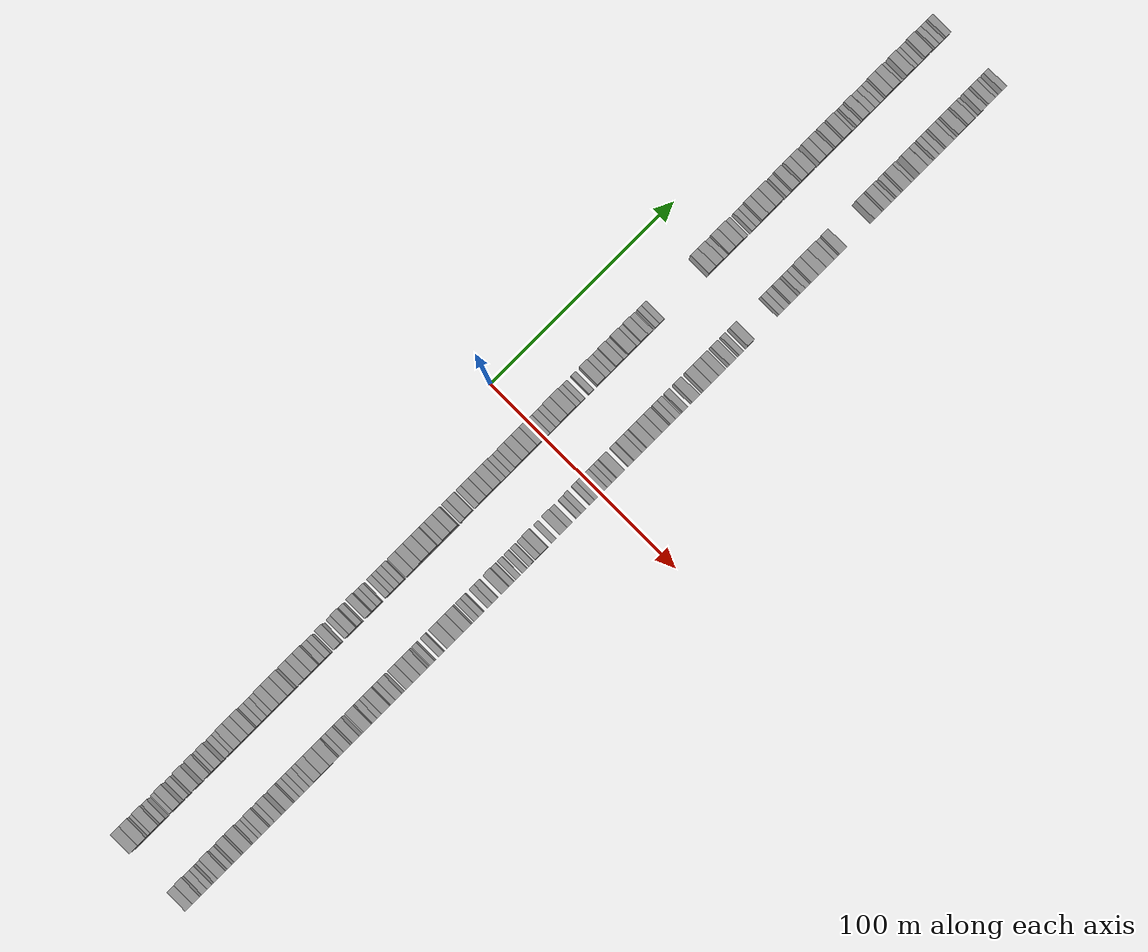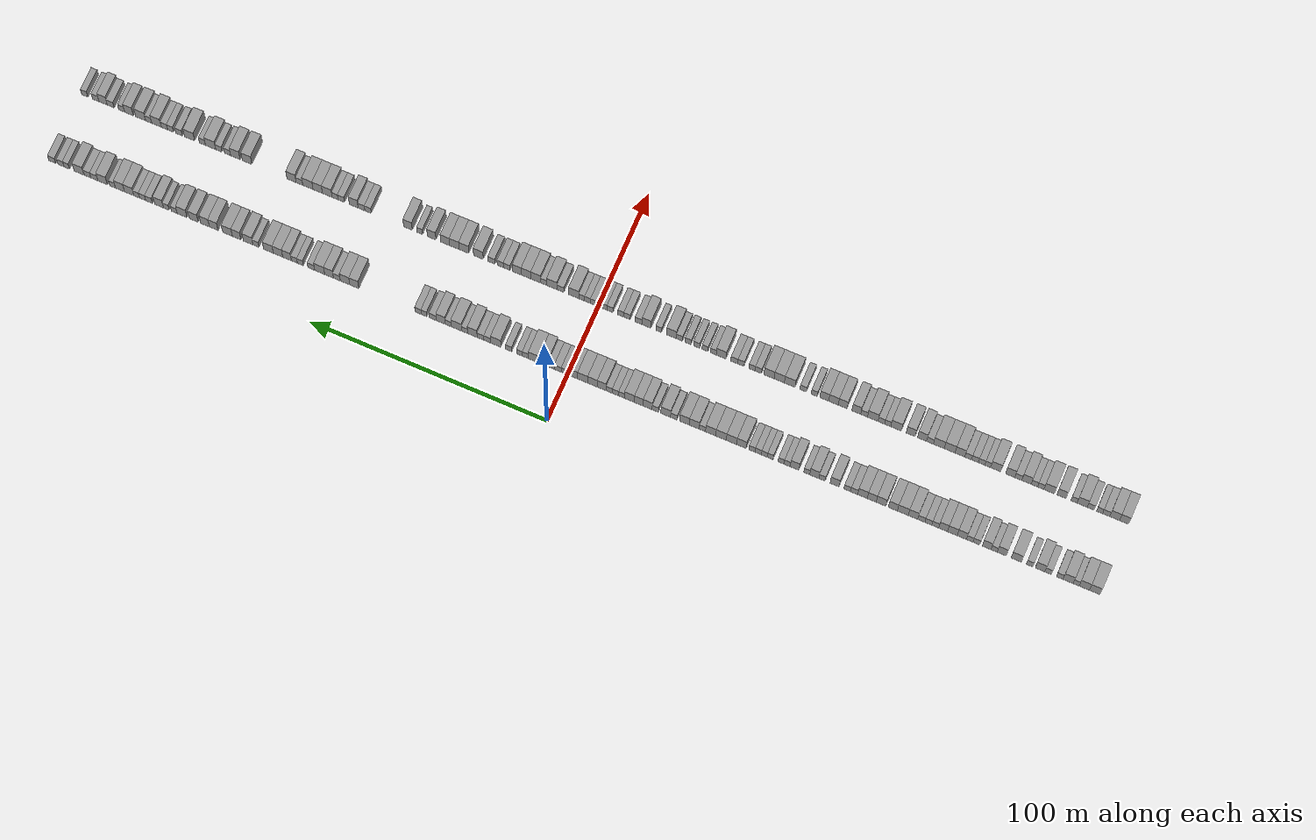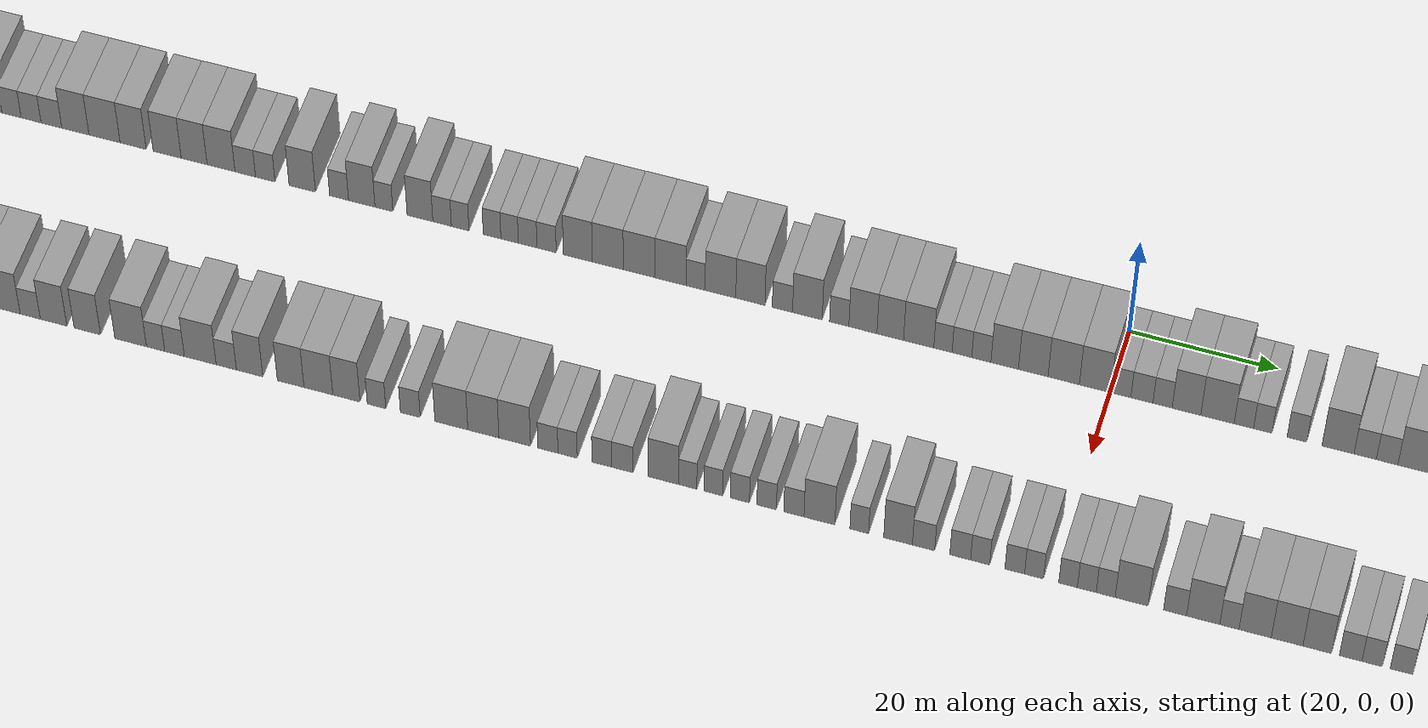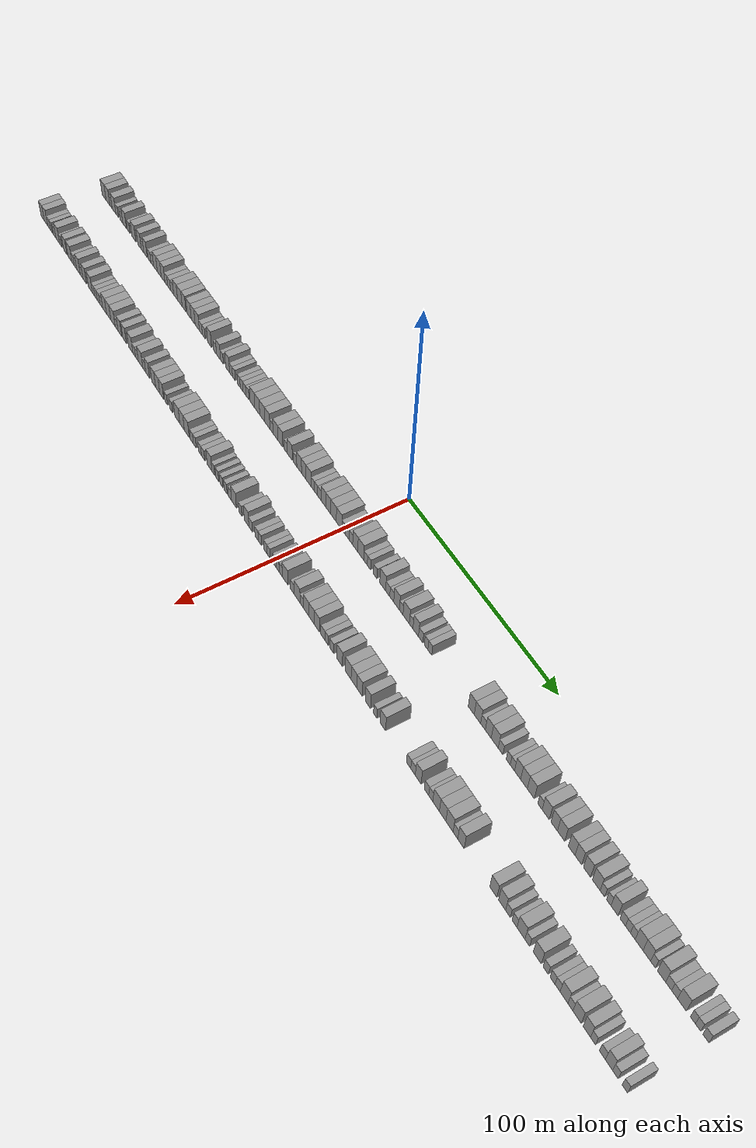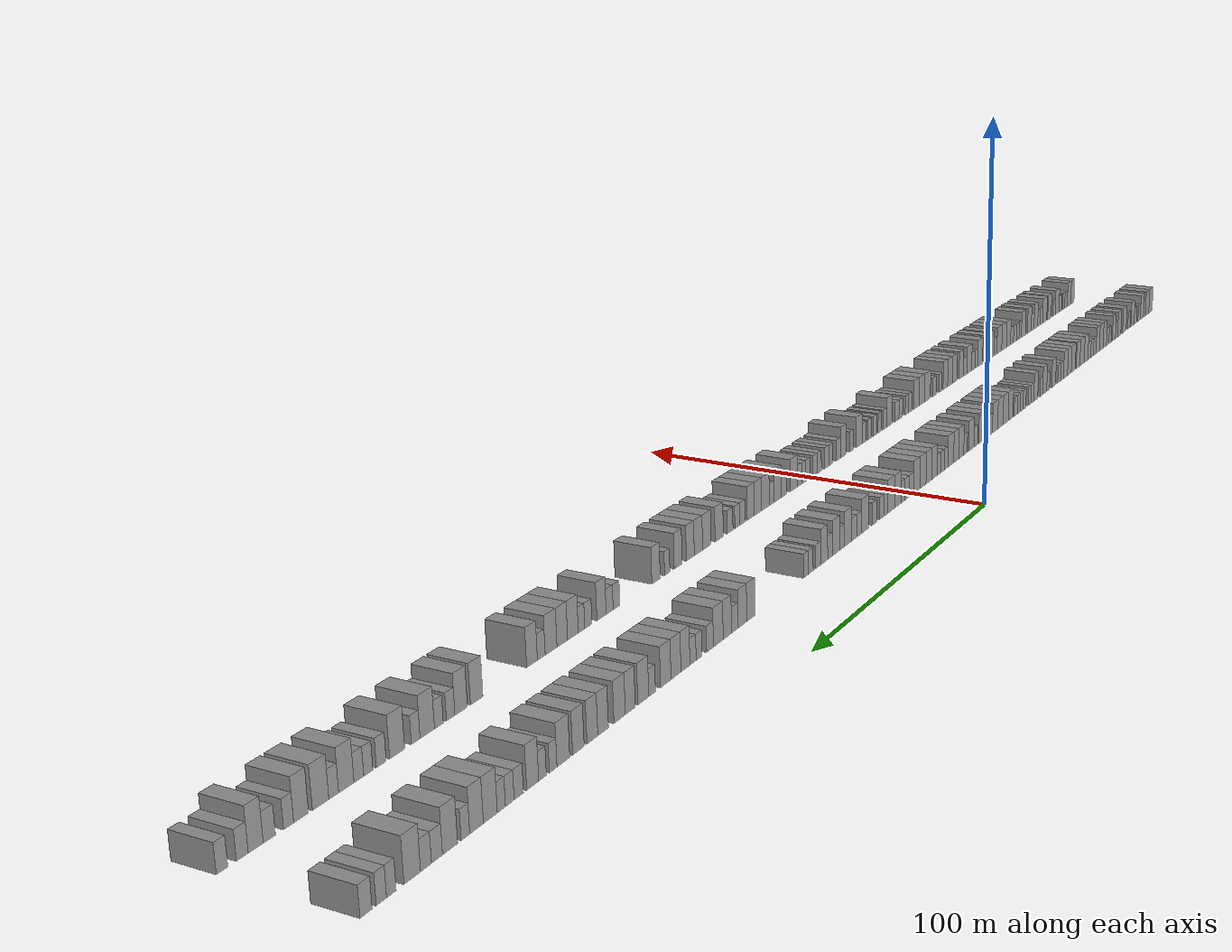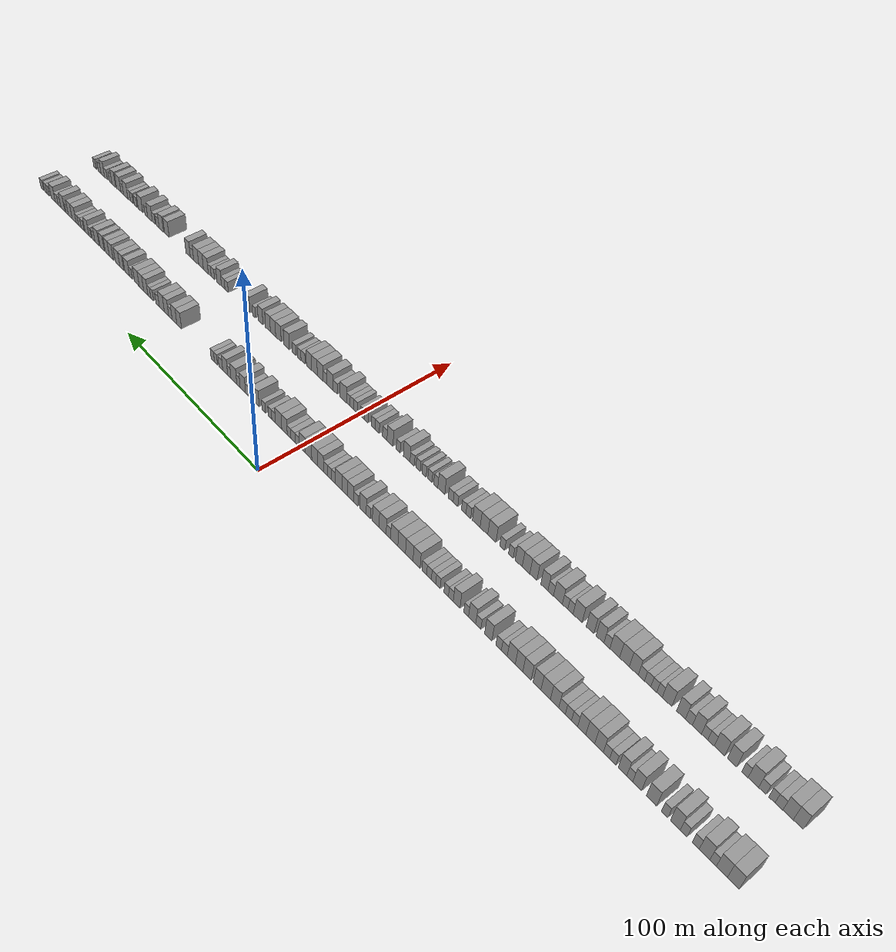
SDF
<sdf version="1.6">
 <world name="default">
  <scene>
   <sky><clouds><speed>12</speed></clouds></sky>
   <ambient>0.4 0.4 0.4 1</ambient>
   <background>0.7 0.7 0.7 1</background>
   <shadows>1</shadows>
  </scene>
  <gravity>0 0 -9.8066</gravity>
  <magnetic_field>6e-06 2.3e-05 -4.2e-05</magnetic_field>
  <physics default="0" name="default_physics" type="ode">
   <ode>
    <solver>
     <type>quick</type>
     <iters>10</iters>
     <sor>1.0</sor>
     <use_dynamic_moi_rescaling>0</use_dynamic_moi_rescaling>
    </solver>
    <constraints>
     <cfm>0</cfm>
     <erp>0.2</erp>
     <contact_max_correcting_vel>100</contact_max_correcting_vel>
     <contact_surface_layer>0.001</contact_surface_layer>
    </constraints>
   </ode>
   <max_step_size>0.004</max_step_size>
   <real_time_factor>1</real_time_factor>
   <real_time_update_rate>250</real_time_update_rate>
  </physics>
  <light name="sun" type="directional">
   <pose>0 0 10 0 0 0</pose>
   <diffuse>0.8 0.8 0.8 1</diffuse>
   <specular>0.2 0.2 0.2 1</specular>
   <attenuation>
    <range>1000</range>
    <constant>0.9</constant>
    <linear>0.01</linear>
    <quadratic>0.001</quadratic>
   </attenuation>
   <direction>-0.5 0.1 -0.9</direction>
  </light>
  <model name="building_1">
   <static>1</static>
   <pose>25.0000 -217.8196 0 0.000000 0.000000 0.000000</pose>
   <link name="link">
    <pose>0 0 4.50 0 0 0</pose>
    <collision name="collision"><geometry><box><size>10.0000 4.3608 9.0000</size></box></geometry></collision>
    <visual name="visual">
     <cast_shadows>0</cast_shadows>
     <geometry><box><size>10.0000 4.3608 9.0000</size></box></geometry>
     <material>
      <script>
       <uri>model://grey_wall/materials/scripts</uri>
       <uri>model://grey_wall/materials/textures</uri>
       <name>vrc/grey_wall</name>
      </script>
     </material>
    </visual>
   </link>
  </model>
  <model name="building_2">
   <static>1</static>
   <pose>25.0000 -213.5517 0 0.000000 0.000000 0.000000</pose>
   <link name="link">
    <pose>0 0 4.50 0 0 0</pose>
    <collision name="collision"><geometry><box><size>10.0000 4.1750 9.0000</size></box></geometry></collision>
    <visual name="visual">
     <cast_shadows>0</cast_shadows>
     <geometry><box><size>10.0000 4.1750 9.0000</size></box></geometry>
     <material>
      <script>
       <uri>model://grey_wall/materials/scripts</uri>
       <uri>model://grey_wall/materials/textures</uri>
       <name>vrc/grey_wall</name>
      </script>
     </material>
    </visual>
   </link>
  </model>
  <model name="building_3">
   <static>1</static>
   <pose>25.0000 -210.2575 0 0.000000 0.000000 0.000000</pose>
   <link name="link">
    <pose>0 0 3.00 0 0 0</pose>
    <collision name="collision"><geometry><box><size>10.0000 2.4133 6.0000</size></box></geometry></collision>
    <visual name="visual">
     <cast_shadows>0</cast_shadows>
     <geometry><box><size>10.0000 2.4133 6.0000</size></box></geometry>
     <material>
      <script>
       <uri>model://grey_wall/materials/scripts</uri>
       <uri>model://grey_wall/materials/textures</uri>
       <name>vrc/grey_wall</name>
      </script>
     </material>
    </visual>
   </link>
  </model>
  <model name="building_4">
   <static>1</static>
   <pose>25.0000 -206.9874 0 0.000000 0.000000 0.000000</pose>
   <link name="link">
    <pose>0 0 4.50 0 0 0</pose>
    <collision name="collision"><geometry><box><size>10.0000 4.1270 9.0000</size></box></geometry></collision>
    <visual name="visual">
     <cast_shadows>0</cast_shadows>
     <geometry><box><size>10.0000 4.1270 9.0000</size></box></geometry>
     <material>
      <script>
       <uri>model://grey_wall/materials/scripts</uri>
       <uri>model://grey_wall/materials/textures</uri>
       <name>vrc/grey_wall</name>
      </script>
     </material>
    </visual>
   </link>
  </model>
  <model name="building_5">
   <static>1</static>
   <pose>25.0000 -203.5547 0 0.000000 0.000000 0.000000</pose>
   <link name="link">
    <pose>0 0 3.00 0 0 0</pose>
    <collision name="collision"><geometry><box><size>10.0000 2.7383 6.0000</size></box></geometry></collision>
    <visual name="visual">
     <cast_shadows>0</cast_shadows>
     <geometry><box><size>10.0000 2.7383 6.0000</size></box></geometry>
     <material>
      <script>
       <uri>model://grey_wall/materials/scripts</uri>
       <uri>model://grey_wall/materials/textures</uri>
       <name>vrc/grey_wall</name>
      </script>
     </material>
    </visual>
   </link>
  </model>
  <model name="building_6">
   <static>1</static>
   <pose>25.0000 -198.8463 0 0.000000 0.000000 0.000000</pose>
   <link name="link">
    <pose>0 0 3.00 0 0 0</pose>
    <collision name="collision"><geometry><box><size>10.0000 2.6786 6.0000</size></box></geometry></collision>
    <visual name="visual">
     <cast_shadows>0</cast_shadows>
     <geometry><box><size>10.0000 2.6786 6.0000</size></box></geometry>
     <material>
      <script>
       <uri>model://grey_wall/materials/scripts</uri>
       <uri>model://grey_wall/materials/textures</uri>
       <name>vrc/grey_wall</name>
      </script>
     </material>
    </visual>
   </link>
  </model>
  <model name="building_7">
   <static>1</static>
   <pose>25.0000 -195.5430 0 0.000000 0.000000 0.000000</pose>
   <link name="link">
    <pose>0 0 4.50 0 0 0</pose>
    <collision name="collision"><geometry><box><size>10.0000 3.9280 9.0000</size></box></geometry></collision>
    <visual name="visual">
     <cast_shadows>0</cast_shadows>
     <geometry><box><size>10.0000 3.9280 9.0000</size></box></geometry>
     <material>
      <script>
       <uri>model://grey_wall/materials/scripts</uri>
       <uri>model://grey_wall/materials/textures</uri>
       <name>vrc/grey_wall</name>
      </script>
     </material>
    </visual>
   </link>
  </model>
  <model name="building_8">
   <static>1</static>
   <pose>25.0000 -191.2647 0 0.000000 0.000000 0.000000</pose>
   <link name="link">
    <pose>0 0 3.00 0 0 0</pose>
    <collision name="collision"><geometry><box><size>10.0000 2.6285 6.0000</size></box></geometry></collision>
    <visual name="visual">
     <cast_shadows>0</cast_shadows>
     <geometry><box><size>10.0000 2.6285 6.0000</size></box></geometry>
     <material>
      <script>
       <uri>model://grey_wall/materials/scripts</uri>
       <uri>model://grey_wall/materials/textures</uri>
       <name>vrc/grey_wall</name>
      </script>
     </material>
    </visual>
   </link>
  </model>
  <model name="building_9">
   <static>1</static>
   <pose>25.0000 -185.8397 0 0.000000 0.000000 0.000000</pose>
   <link name="link">
    <pose>0 0 4.50 0 0 0</pose>
    <collision name="collision"><geometry><box><size>10.0000 4.2216 9.0000</size></box></geometry></collision>
    <visual name="visual">
     <cast_shadows>0</cast_shadows>
     <geometry><box><size>10.0000 4.2216 9.0000</size></box></geometry>
     <material>
      <script>
       <uri>model://grey_wall/materials/scripts</uri>
       <uri>model://grey_wall/materials/textures</uri>
       <name>vrc/grey_wall</name>
      </script>
     </material>
    </visual>
   </link>
  </model>
  <model name="building_10">
   <static>1</static>
   <pose>25.0000 -179.8683 0 0.000000 0.000000 0.000000</pose>
   <link name="link">
    <pose>0 0 4.50 0 0 0</pose>
    <collision name="collision"><geometry><box><size>10.0000 3.7211 9.0000</size></box></geometry></collision>
    <visual name="visual">
     <cast_shadows>0</cast_shadows>
     <geometry><box><size>10.0000 3.7211 9.0000</size></box></geometry>
     <material>
      <script>
       <uri>model://grey_wall/materials/scripts</uri>
       <uri>model://grey_wall/materials/textures</uri>
       <name>vrc/grey_wall</name>
      </script>
     </material>
    </visual>
   </link>
  </model>
  <model name="building_11">
   <static>1</static>
   <pose>25.0000 -176.7563 0 0.000000 0.000000 0.000000</pose>
   <link name="link">
    <pose>0 0 3.00 0 0 0</pose>
    <collision name="collision"><geometry><box><size>10.0000 2.5028 6.0000</size></box></geometry></collision>
    <visual name="visual">
     <cast_shadows>0</cast_shadows>
     <geometry><box><size>10.0000 2.5028 6.0000</size></box></geometry>
     <material>
      <script>
       <uri>model://grey_wall/materials/scripts</uri>
       <uri>model://grey_wall/materials/textures</uri>
       <name>vrc/grey_wall</name>
      </script>
     </material>
    </visual>
   </link>
  </model>
  <model name="building_12">
   <static>1</static>
   <pose>25.0000 -173.7009 0 0.000000 0.000000 0.000000</pose>
   <link name="link">
    <pose>0 0 4.50 0 0 0</pose>
    <collision name="collision"><geometry><box><size>10.0000 3.6080 9.0000</size></box></geometry></collision>
    <visual name="visual">
     <cast_shadows>0</cast_shadows>
     <geometry><box><size>10.0000 3.6080 9.0000</size></box></geometry>
     <material>
      <script>
       <uri>model://grey_wall/materials/scripts</uri>
       <uri>model://grey_wall/materials/textures</uri>
       <name>vrc/grey_wall</name>
      </script>
     </material>
    </visual>
   </link>
  </model>
  <model name="building_13">
   <static>1</static>
   <pose>25.0000 -169.5221 0 0.000000 0.000000 0.000000</pose>
   <link name="link">
    <pose>0 0 3.00 0 0 0</pose>
    <collision name="collision"><geometry><box><size>10.0000 2.7497 6.0000</size></box></geometry></collision>
    <visual name="visual">
     <cast_shadows>0</cast_shadows>
     <geometry><box><size>10.0000 2.7497 6.0000</size></box></geometry>
     <material>
      <script>
       <uri>model://grey_wall/materials/scripts</uri>
       <uri>model://grey_wall/materials/textures</uri>
       <name>vrc/grey_wall</name>
      </script>
     </material>
    </visual>
   </link>
  </model>
  <model name="building_14">
   <static>1</static>
   <pose>25.0000 -166.7844 0 0.000000 0.000000 0.000000</pose>
   <link name="link">
    <pose>0 0 3.00 0 0 0</pose>
    <collision name="collision"><geometry><box><size>10.0000 2.7257 6.0000</size></box></geometry></collision>
    <visual name="visual">
     <cast_shadows>0</cast_shadows>
     <geometry><box><size>10.0000 2.7257 6.0000</size></box></geometry>
     <material>
      <script>
       <uri>model://grey_wall/materials/scripts</uri>
       <uri>model://grey_wall/materials/textures</uri>
       <name>vrc/grey_wall</name>
      </script>
     </material>
    </visual>
   </link>
  </model>
  <model name="building_15">
   <static>1</static>
   <pose>25.0000 -163.5337 0 0.000000 0.000000 0.000000</pose>
   <link name="link">
    <pose>0 0 4.50 0 0 0</pose>
    <collision name="collision"><geometry><box><size>10.0000 3.7757 9.0000</size></box></geometry></collision>
    <visual name="visual">
     <cast_shadows>0</cast_shadows>
     <geometry><box><size>10.0000 3.7757 9.0000</size></box></geometry>
     <material>
      <script>
       <uri>model://grey_wall/materials/scripts</uri>
       <uri>model://grey_wall/materials/textures</uri>
       <name>vrc/grey_wall</name>
      </script>
     </material>
    </visual>
   </link>
  </model>
  <model name="building_16">
   <static>1</static>
   <pose>25.0000 -159.6657 0 0.000000 0.000000 0.000000</pose>
   <link name="link">
    <pose>0 0 4.50 0 0 0</pose>
    <collision name="collision"><geometry><box><size>10.0000 3.9602 9.0000</size></box></geometry></collision>
    <visual name="visual">
     <cast_shadows>0</cast_shadows>
     <geometry><box><size>10.0000 3.9602 9.0000</size></box></geometry>
     <material>
      <script>
       <uri>model://grey_wall/materials/scripts</uri>
       <uri>model://grey_wall/materials/textures</uri>
       <name>vrc/grey_wall</name>
      </script>
     </material>
    </visual>
   </link>
  </model>
  <model name="building_17">
   <static>1</static>
   <pose>25.0000 -155.8524 0 0.000000 0.000000 0.000000</pose>
   <link name="link">
    <pose>0 0 4.50 0 0 0</pose>
    <collision name="collision"><geometry><box><size>10.0000 3.6663 9.0000</size></box></geometry></collision>
    <visual name="visual">
     <cast_shadows>0</cast_shadows>
     <geometry><box><size>10.0000 3.6663 9.0000</size></box></geometry>
     <material>
      <script>
       <uri>model://grey_wall/materials/scripts</uri>
       <uri>model://grey_wall/materials/textures</uri>
       <name>vrc/grey_wall</name>
      </script>
     </material>
    </visual>
   </link>
  </model>
  <model name="building_18">
   <static>1</static>
   <pose>25.0000 -152.6347 0 0.000000 0.000000 0.000000</pose>
   <link name="link">
    <pose>0 0 3.00 0 0 0</pose>
    <collision name="collision"><geometry><box><size>10.0000 2.7692 6.0000</size></box></geometry></collision>
    <visual name="visual">
     <cast_shadows>0</cast_shadows>
     <geometry><box><size>10.0000 2.7692 6.0000</size></box></geometry>
     <material>
      <script>
       <uri>model://grey_wall/materials/scripts</uri>
       <uri>model://grey_wall/materials/textures</uri>
       <name>vrc/grey_wall</name>
      </script>
     </material>
    </visual>
   </link>
  </model>
  <model name="building_19">
   <static>1</static>
   <pose>25.0000 -149.8208 0 0.000000 0.000000 0.000000</pose>
   <link name="link">
    <pose>0 0 3.00 0 0 0</pose>
    <collision name="collision"><geometry><box><size>10.0000 2.8584 6.0000</size></box></geometry></collision>
    <visual name="visual">
     <cast_shadows>0</cast_shadows>
     <geometry><box><size>10.0000 2.8584 6.0000</size></box></geometry>
     <material>
      <script>
       <uri>model://grey_wall/materials/scripts</uri>
       <uri>model://grey_wall/materials/textures</uri>
       <name>vrc/grey_wall</name>
      </script>
     </material>
    </visual>
   </link>
  </model>
  <model name="building_20">
   <static>1</static>
   <pose>25.0000 -146.8978 0 0.000000 0.000000 0.000000</pose>
   <link name="link">
    <pose>0 0 3.00 0 0 0</pose>
    <collision name="collision"><geometry><box><size>10.0000 2.9875 6.0000</size></box></geometry></collision>
    <visual name="visual">
     <cast_shadows>0</cast_shadows>
     <geometry><box><size>10.0000 2.9875 6.0000</size></box></geometry>
     <material>
      <script>
       <uri>model://grey_wall/materials/scripts</uri>
       <uri>model://grey_wall/materials/textures</uri>
       <name>vrc/grey_wall</name>
      </script>
     </material>
    </visual>
   </link>
  </model>
  <model name="building_21">
   <static>1</static>
   <pose>25.0000 -143.4549 0 0.000000 0.000000 0.000000</pose>
   <link name="link">
    <pose>0 0 4.50 0 0 0</pose>
    <collision name="collision"><geometry><box><size>10.0000 3.8983 9.0000</size></box></geometry></collision>
    <visual name="visual">
     <cast_shadows>0</cast_shadows>
     <geometry><box><size>10.0000 3.8983 9.0000</size></box></geometry>
     <material>
      <script>
       <uri>model://grey_wall/materials/scripts</uri>
       <uri>model://grey_wall/materials/textures</uri>
       <name>vrc/grey_wall</name>
      </script>
     </material>
    </visual>
   </link>
  </model>
  <model name="building_22">
   <static>1</static>
   <pose>25.0000 -139.2806 0 0.000000 0.000000 0.000000</pose>
   <link name="link">
    <pose>0 0 4.50 0 0 0</pose>
    <collision name="collision"><geometry><box><size>10.0000 4.4503 9.0000</size></box></geometry></collision>
    <visual name="visual">
     <cast_shadows>0</cast_shadows>
     <geometry><box><size>10.0000 4.4503 9.0000</size></box></geometry>
     <material>
      <script>
       <uri>model://grey_wall/materials/scripts</uri>
       <uri>model://grey_wall/materials/textures</uri>
       <name>vrc/grey_wall</name>
      </script>
     </material>
    </visual>
   </link>
  </model>
  <model name="building_23">
   <static>1</static>
   <pose>25.0000 -135.1921 0 0.000000 0.000000 0.000000</pose>
   <link name="link">
    <pose>0 0 4.50 0 0 0</pose>
    <collision name="collision"><geometry><box><size>10.0000 3.7267 9.0000</size></box></geometry></collision>
    <visual name="visual">
     <cast_shadows>0</cast_shadows>
     <geometry><box><size>10.0000 3.7267 9.0000</size></box></geometry>
     <material>
      <script>
       <uri>model://grey_wall/materials/scripts</uri>
       <uri>model://grey_wall/materials/textures</uri>
       <name>vrc/grey_wall</name>
      </script>
     </material>
    </visual>
   </link>
  </model>
  <model name="building_24">
   <static>1</static>
   <pose>25.0000 -130.3292 0 0.000000 0.000000 0.000000</pose>
   <link name="link">
    <pose>0 0 4.50 0 0 0</pose>
    <collision name="collision"><geometry><box><size>10.0000 3.9993 9.0000</size></box></geometry></collision>
    <visual name="visual">
     <cast_shadows>0</cast_shadows>
     <geometry><box><size>10.0000 3.9993 9.0000</size></box></geometry>
     <material>
      <script>
       <uri>model://grey_wall/materials/scripts</uri>
       <uri>model://grey_wall/materials/textures</uri>
       <name>vrc/grey_wall</name>
      </script>
     </material>
    </visual>
   </link>
  </model>
  <model name="building_25">
   <static>1</static>
   <pose>25.0000 -126.4850 0 0.000000 0.000000 0.000000</pose>
   <link name="link">
    <pose>0 0 4.50 0 0 0</pose>
    <collision name="collision"><geometry><box><size>10.0000 3.6889 9.0000</size></box></geometry></collision>
    <visual name="visual">
     <cast_shadows>0</cast_shadows>
     <geometry><box><size>10.0000 3.6889 9.0000</size></box></geometry>
     <material>
      <script>
       <uri>model://grey_wall/materials/scripts</uri>
       <uri>model://grey_wall/materials/textures</uri>
       <name>vrc/grey_wall</name>
      </script>
     </material>
    </visual>
   </link>
  </model>
  <model name="building_26">
   <static>1</static>
   <pose>25.0000 -122.6593 0 0.000000 0.000000 0.000000</pose>
   <link name="link">
    <pose>0 0 4.50 0 0 0</pose>
    <collision name="collision"><geometry><box><size>10.0000 3.9626 9.0000</size></box></geometry></collision>
    <visual name="visual">
     <cast_shadows>0</cast_shadows>
     <geometry><box><size>10.0000 3.9626 9.0000</size></box></geometry>
     <material>
      <script>
       <uri>model://grey_wall/materials/scripts</uri>
       <uri>model://grey_wall/materials/textures</uri>
       <name>vrc/grey_wall</name>
      </script>
     </material>
    </visual>
   </link>
  </model>
  <model name="building_27">
   <static>1</static>
   <pose>25.0000 -119.2190 0 0.000000 0.000000 0.000000</pose>
   <link name="link">
    <pose>0 0 3.00 0 0 0</pose>
    <collision name="collision"><geometry><box><size>10.0000 2.9181 6.0000</size></box></geometry></collision>
    <visual name="visual">
     <cast_shadows>0</cast_shadows>
     <geometry><box><size>10.0000 2.9181 6.0000</size></box></geometry>
     <material>
      <script>
       <uri>model://grey_wall/materials/scripts</uri>
       <uri>model://grey_wall/materials/textures</uri>
       <name>vrc/grey_wall</name>
      </script>
     </material>
    </visual>
   </link>
  </model>
  <model name="building_28">
   <static>1</static>
   <pose>25.0000 -116.3828 0 0.000000 0.000000 0.000000</pose>
   <link name="link">
    <pose>0 0 3.00 0 0 0</pose>
    <collision name="collision"><geometry><box><size>10.0000 2.7541 6.0000</size></box></geometry></collision>
    <visual name="visual">
     <cast_shadows>0</cast_shadows>
     <geometry><box><size>10.0000 2.7541 6.0000</size></box></geometry>
     <material>
      <script>
       <uri>model://grey_wall/materials/scripts</uri>
       <uri>model://grey_wall/materials/textures</uri>
       <name>vrc/grey_wall</name>
      </script>
     </material>
    </visual>
   </link>
  </model>
  <model name="building_29">
   <static>1</static>
   <pose>25.0000 -111.1421 0 0.000000 0.000000 0.000000</pose>
   <link name="link">
    <pose>0 0 4.50 0 0 0</pose>
    <collision name="collision"><geometry><box><size>10.0000 3.7273 9.0000</size></box></geometry></collision>
    <visual name="visual">
     <cast_shadows>0</cast_shadows>
     <geometry><box><size>10.0000 3.7273 9.0000</size></box></geometry>
     <material>
      <script>
       <uri>model://grey_wall/materials/scripts</uri>
       <uri>model://grey_wall/materials/textures</uri>
       <name>vrc/grey_wall</name>
      </script>
     </material>
    </visual>
   </link>
  </model>
  <model name="building_30">
   <static>1</static>
   <pose>25.0000 -105.9499 0 0.000000 0.000000 0.000000</pose>
   <link name="link">
    <pose>0 0 3.00 0 0 0</pose>
    <collision name="collision"><geometry><box><size>10.0000 2.6573 6.0000</size></box></geometry></collision>
    <visual name="visual">
     <cast_shadows>0</cast_shadows>
     <geometry><box><size>10.0000 2.6573 6.0000</size></box></geometry>
     <material>
      <script>
       <uri>model://grey_wall/materials/scripts</uri>
       <uri>model://grey_wall/materials/textures</uri>
       <name>vrc/grey_wall</name>
      </script>
     </material>
    </visual>
   </link>
  </model>
  <model name="building_31">
   <static>1</static>
   <pose>25.0000 -102.7578 0 0.000000 0.000000 0.000000</pose>
   <link name="link">
    <pose>0 0 4.50 0 0 0</pose>
    <collision name="collision"><geometry><box><size>10.0000 3.7269 9.0000</size></box></geometry></collision>
    <visual name="visual">
     <cast_shadows>0</cast_shadows>
     <geometry><box><size>10.0000 3.7269 9.0000</size></box></geometry>
     <material>
      <script>
       <uri>model://grey_wall/materials/scripts</uri>
       <uri>model://grey_wall/materials/textures</uri>
       <name>vrc/grey_wall</name>
      </script>
     </material>
    </visual>
   </link>
  </model>
  <model name="building_32">
   <static>1</static>
   <pose>25.0000 -99.6385 0 0.000000 0.000000 0.000000</pose>
   <link name="link">
    <pose>0 0 3.00 0 0 0</pose>
    <collision name="collision"><geometry><box><size>10.0000 2.5117 6.0000</size></box></geometry></collision>
    <visual name="visual">
     <cast_shadows>0</cast_shadows>
     <geometry><box><size>10.0000 2.5117 6.0000</size></box></geometry>
     <material>
      <script>
       <uri>model://grey_wall/materials/scripts</uri>
       <uri>model://grey_wall/materials/textures</uri>
       <name>vrc/grey_wall</name>
      </script>
     </material>
    </visual>
   </link>
  </model>
  <model name="building_33">
   <static>1</static>
   <pose>25.0000 -94.5818 0 0.000000 0.000000 0.000000</pose>
   <link name="link">
    <pose>0 0 4.50 0 0 0</pose>
    <collision name="collision"><geometry><box><size>10.0000 3.6016 9.0000</size></box></geometry></collision>
    <visual name="visual">
     <cast_shadows>0</cast_shadows>
     <geometry><box><size>10.0000 3.6016 9.0000</size></box></geometry>
     <material>
      <script>
       <uri>model://grey_wall/materials/scripts</uri>
       <uri>model://grey_wall/materials/textures</uri>
       <name>vrc/grey_wall</name>
      </script>
     </material>
    </visual>
   </link>
  </model>
  <model name="building_34">
   <static>1</static>
   <pose>25.0000 -91.4817 0 0.000000 0.000000 0.000000</pose>
   <link name="link">
    <pose>0 0 3.00 0 0 0</pose>
    <collision name="collision"><geometry><box><size>10.0000 2.5986 6.0000</size></box></geometry></collision>
    <visual name="visual">
     <cast_shadows>0</cast_shadows>
     <geometry><box><size>10.0000 2.5986 6.0000</size></box></geometry>
     <material>
      <script>
       <uri>model://grey_wall/materials/scripts</uri>
       <uri>model://grey_wall/materials/textures</uri>
       <name>vrc/grey_wall</name>
      </script>
     </material>
    </visual>
   </link>
  </model>
  <model name="building_35">
   <static>1</static>
   <pose>25.0000 -88.9547 0 0.000000 0.000000 0.000000</pose>
   <link name="link">
    <pose>0 0 3.00 0 0 0</pose>
    <collision name="collision"><geometry><box><size>10.0000 2.4553 6.0000</size></box></geometry></collision>
    <visual name="visual">
     <cast_shadows>0</cast_shadows>
     <geometry><box><size>10.0000 2.4553 6.0000</size></box></geometry>
     <material>
      <script>
       <uri>model://grey_wall/materials/scripts</uri>
       <uri>model://grey_wall/materials/textures</uri>
       <name>vrc/grey_wall</name>
      </script>
     </material>
    </visual>
   </link>
  </model>
  <model name="building_36">
   <static>1</static>
   <pose>25.0000 -84.4982 0 0.000000 0.000000 0.000000</pose>
   <link name="link">
    <pose>0 0 3.00 0 0 0</pose>
    <collision name="collision"><geometry><box><size>10.0000 2.4577 6.0000</size></box></geometry></collision>
    <visual name="visual">
     <cast_shadows>0</cast_shadows>
     <geometry><box><size>10.0000 2.4577 6.0000</size></box></geometry>
     <material>
      <script>
       <uri>model://grey_wall/materials/scripts</uri>
       <uri>model://grey_wall/materials/textures</uri>
       <name>vrc/grey_wall</name>
      </script>
     </material>
    </visual>
   </link>
  </model>
  <model name="building_37">
   <static>1</static>
   <pose>25.0000 -82.0529 0 0.000000 0.000000 0.000000</pose>
   <link name="link">
    <pose>0 0 3.00 0 0 0</pose>
    <collision name="collision"><geometry><box><size>10.0000 2.4330 6.0000</size></box></geometry></collision>
    <visual name="visual">
     <cast_shadows>0</cast_shadows>
     <geometry><box><size>10.0000 2.4330 6.0000</size></box></geometry>
     <material>
      <script>
       <uri>model://grey_wall/materials/scripts</uri>
       <uri>model://grey_wall/materials/textures</uri>
       <name>vrc/grey_wall</name>
      </script>
     </material>
    </visual>
   </link>
  </model>
  <model name="building_38">
   <static>1</static>
   <pose>25.0000 -79.5354 0 0.000000 0.000000 0.000000</pose>
   <link name="link">
    <pose>0 0 3.00 0 0 0</pose>
    <collision name="collision"><geometry><box><size>10.0000 2.6020 6.0000</size></box></geometry></collision>
    <visual name="visual">
     <cast_shadows>0</cast_shadows>
     <geometry><box><size>10.0000 2.6020 6.0000</size></box></geometry>
     <material>
      <script>
       <uri>model://grey_wall/materials/scripts</uri>
       <uri>model://grey_wall/materials/textures</uri>
       <name>vrc/grey_wall</name>
      </script>
     </material>
    </visual>
   </link>
  </model>
  <model name="building_39">
   <static>1</static>
   <pose>25.0000 -76.9047 0 0.000000 0.000000 0.000000</pose>
   <link name="link">
    <pose>0 0 3.00 0 0 0</pose>
    <collision name="collision"><geometry><box><size>10.0000 2.6593 6.0000</size></box></geometry></collision>
    <visual name="visual">
     <cast_shadows>0</cast_shadows>
     <geometry><box><size>10.0000 2.6593 6.0000</size></box></geometry>
     <material>
      <script>
       <uri>model://grey_wall/materials/scripts</uri>
       <uri>model://grey_wall/materials/textures</uri>
       <name>vrc/grey_wall</name>
      </script>
     </material>
    </visual>
   </link>
  </model>
  <model name="building_40">
   <static>1</static>
   <pose>25.0000 -72.5668 0 0.000000 0.000000 0.000000</pose>
   <link name="link">
    <pose>0 0 4.50 0 0 0</pose>
    <collision name="collision"><geometry><box><size>10.0000 4.0165 9.0000</size></box></geometry></collision>
    <visual name="visual">
     <cast_shadows>0</cast_shadows>
     <geometry><box><size>10.0000 4.0165 9.0000</size></box></geometry>
     <material>
      <script>
       <uri>model://grey_wall/materials/scripts</uri>
       <uri>model://grey_wall/materials/textures</uri>
       <name>vrc/grey_wall</name>
      </script>
     </material>
    </visual>
   </link>
  </model>
  <model name="building_41">
   <static>1</static>
   <pose>25.0000 -68.4101 0 0.000000 0.000000 0.000000</pose>
   <link name="link">
    <pose>0 0 4.50 0 0 0</pose>
    <collision name="collision"><geometry><box><size>10.0000 4.2969 9.0000</size></box></geometry></collision>
    <visual name="visual">
     <cast_shadows>0</cast_shadows>
     <geometry><box><size>10.0000 4.2969 9.0000</size></box></geometry>
     <material>
      <script>
       <uri>model://grey_wall/materials/scripts</uri>
       <uri>model://grey_wall/materials/textures</uri>
       <name>vrc/grey_wall</name>
      </script>
     </material>
    </visual>
   </link>
  </model>
  <model name="building_42">
   <static>1</static>
   <pose>25.0000 -64.0627 0 0.000000 0.000000 0.000000</pose>
   <link name="link">
    <pose>0 0 4.50 0 0 0</pose>
    <collision name="collision"><geometry><box><size>10.0000 4.3979 9.0000</size></box></geometry></collision>
    <visual name="visual">
     <cast_shadows>0</cast_shadows>
     <geometry><box><size>10.0000 4.3979 9.0000</size></box></geometry>
     <material>
      <script>
       <uri>model://grey_wall/materials/scripts</uri>
       <uri>model://grey_wall/materials/textures</uri>
       <name>vrc/grey_wall</name>
      </script>
     </material>
    </visual>
   </link>
  </model>
  <model name="building_43">
   <static>1</static>
   <pose>25.0000 -59.7352 0 0.000000 0.000000 0.000000</pose>
   <link name="link">
    <pose>0 0 4.50 0 0 0</pose>
    <collision name="collision"><geometry><box><size>10.0000 4.2573 9.0000</size></box></geometry></collision>
    <visual name="visual">
     <cast_shadows>0</cast_shadows>
     <geometry><box><size>10.0000 4.2573 9.0000</size></box></geometry>
     <material>
      <script>
       <uri>model://grey_wall/materials/scripts</uri>
       <uri>model://grey_wall/materials/textures</uri>
       <name>vrc/grey_wall</name>
      </script>
     </material>
    </visual>
   </link>
  </model>
  <model name="building_44">
   <static>1</static>
   <pose>25.0000 -56.2948 0 0.000000 0.000000 0.000000</pose>
   <link name="link">
    <pose>0 0 3.00 0 0 0</pose>
    <collision name="collision"><geometry><box><size>10.0000 2.6233 6.0000</size></box></geometry></collision>
    <visual name="visual">
     <cast_shadows>0</cast_shadows>
     <geometry><box><size>10.0000 2.6233 6.0000</size></box></geometry>
     <material>
      <script>
       <uri>model://grey_wall/materials/scripts</uri>
       <uri>model://grey_wall/materials/textures</uri>
       <name>vrc/grey_wall</name>
      </script>
     </material>
    </visual>
   </link>
  </model>
  <model name="building_45">
   <static>1</static>
   <pose>25.0000 -52.8796 0 0.000000 0.000000 0.000000</pose>
   <link name="link">
    <pose>0 0 4.50 0 0 0</pose>
    <collision name="collision"><geometry><box><size>10.0000 4.2071 9.0000</size></box></geometry></collision>
    <visual name="visual">
     <cast_shadows>0</cast_shadows>
     <geometry><box><size>10.0000 4.2071 9.0000</size></box></geometry>
     <material>
      <script>
       <uri>model://grey_wall/materials/scripts</uri>
       <uri>model://grey_wall/materials/textures</uri>
       <name>vrc/grey_wall</name>
      </script>
     </material>
    </visual>
   </link>
  </model>
  <model name="building_46">
   <static>1</static>
   <pose>25.0000 -48.7759 0 0.000000 0.000000 0.000000</pose>
   <link name="link">
    <pose>0 0 4.50 0 0 0</pose>
    <collision name="collision"><geometry><box><size>10.0000 4.0003 9.0000</size></box></geometry></collision>
    <visual name="visual">
     <cast_shadows>0</cast_shadows>
     <geometry><box><size>10.0000 4.0003 9.0000</size></box></geometry>
     <material>
      <script>
       <uri>model://grey_wall/materials/scripts</uri>
       <uri>model://grey_wall/materials/textures</uri>
       <name>vrc/grey_wall</name>
      </script>
     </material>
    </visual>
   </link>
  </model>
  <model name="building_47">
   <static>1</static>
   <pose>25.0000 -44.3915 0 0.000000 0.000000 0.000000</pose>
   <link name="link">
    <pose>0 0 3.00 0 0 0</pose>
    <collision name="collision"><geometry><box><size>10.0000 2.7683 6.0000</size></box></geometry></collision>
    <visual name="visual">
     <cast_shadows>0</cast_shadows>
     <geometry><box><size>10.0000 2.7683 6.0000</size></box></geometry>
     <material>
      <script>
       <uri>model://grey_wall/materials/scripts</uri>
       <uri>model://grey_wall/materials/textures</uri>
       <name>vrc/grey_wall</name>
      </script>
     </material>
    </visual>
   </link>
  </model>
  <model name="building_48">
   <static>1</static>
   <pose>25.0000 -40.9824 0 0.000000 0.000000 0.000000</pose>
   <link name="link">
    <pose>0 0 4.50 0 0 0</pose>
    <collision name="collision"><geometry><box><size>10.0000 4.0500 9.0000</size></box></geometry></collision>
    <visual name="visual">
     <cast_shadows>0</cast_shadows>
     <geometry><box><size>10.0000 4.0500 9.0000</size></box></geometry>
     <material>
      <script>
       <uri>model://grey_wall/materials/scripts</uri>
       <uri>model://grey_wall/materials/textures</uri>
       <name>vrc/grey_wall</name>
      </script>
     </material>
    </visual>
   </link>
  </model>
  <model name="building_49">
   <static>1</static>
   <pose>25.0000 -36.6390 0 0.000000 0.000000 0.000000</pose>
   <link name="link">
    <pose>0 0 3.00 0 0 0</pose>
    <collision name="collision"><geometry><box><size>10.0000 2.6367 6.0000</size></box></geometry></collision>
    <visual name="visual">
     <cast_shadows>0</cast_shadows>
     <geometry><box><size>10.0000 2.6367 6.0000</size></box></geometry>
     <material>
      <script>
       <uri>model://grey_wall/materials/scripts</uri>
       <uri>model://grey_wall/materials/textures</uri>
       <name>vrc/grey_wall</name>
      </script>
     </material>
    </visual>
   </link>
  </model>
  <model name="building_50">
   <static>1</static>
   <pose>25.0000 -33.4120 0 0.000000 0.000000 0.000000</pose>
   <link name="link">
    <pose>0 0 4.50 0 0 0</pose>
    <collision name="collision"><geometry><box><size>10.0000 3.8174 9.0000</size></box></geometry></collision>
    <visual name="visual">
     <cast_shadows>0</cast_shadows>
     <geometry><box><size>10.0000 3.8174 9.0000</size></box></geometry>
     <material>
      <script>
       <uri>model://grey_wall/materials/scripts</uri>
       <uri>model://grey_wall/materials/textures</uri>
       <name>vrc/grey_wall</name>
      </script>
     </material>
    </visual>
   </link>
  </model>
  <model name="building_51">
   <static>1</static>
   <pose>25.0000 -29.6957 0 0.000000 0.000000 0.000000</pose>
   <link name="link">
    <pose>0 0 4.50 0 0 0</pose>
    <collision name="collision"><geometry><box><size>10.0000 3.6152 9.0000</size></box></geometry></collision>
    <visual name="visual">
     <cast_shadows>0</cast_shadows>
     <geometry><box><size>10.0000 3.6152 9.0000</size></box></geometry>
     <material>
      <script>
       <uri>model://grey_wall/materials/scripts</uri>
       <uri>model://grey_wall/materials/textures</uri>
       <name>vrc/grey_wall</name>
      </script>
     </material>
    </visual>
   </link>
  </model>
  <model name="building_52">
   <static>1</static>
   <pose>25.0000 -25.8387 0 0.000000 0.000000 0.000000</pose>
   <link name="link">
    <pose>0 0 4.50 0 0 0</pose>
    <collision name="collision"><geometry><box><size>10.0000 4.0989 9.0000</size></box></geometry></collision>
    <visual name="visual">
     <cast_shadows>0</cast_shadows>
     <geometry><box><size>10.0000 4.0989 9.0000</size></box></geometry>
     <material>
      <script>
       <uri>model://grey_wall/materials/scripts</uri>
       <uri>model://grey_wall/materials/textures</uri>
       <name>vrc/grey_wall</name>
      </script>
     </material>
    </visual>
   </link>
  </model>
  <model name="building_53">
   <static>1</static>
   <pose>25.0000 -22.5500 0 0.000000 0.000000 0.000000</pose>
   <link name="link">
    <pose>0 0 3.00 0 0 0</pose>
    <collision name="collision"><geometry><box><size>10.0000 2.4784 6.0000</size></box></geometry></collision>
    <visual name="visual">
     <cast_shadows>0</cast_shadows>
     <geometry><box><size>10.0000 2.4784 6.0000</size></box></geometry>
     <material>
      <script>
       <uri>model://grey_wall/materials/scripts</uri>
       <uri>model://grey_wall/materials/textures</uri>
       <name>vrc/grey_wall</name>
      </script>
     </material>
    </visual>
   </link>
  </model>
  <model name="building_54">
   <static>1</static>
   <pose>25.0000 -19.9848 0 0.000000 0.000000 0.000000</pose>
   <link name="link">
    <pose>0 0 3.00 0 0 0</pose>
    <collision name="collision"><geometry><box><size>10.0000 2.6522 6.0000</size></box></geometry></collision>
    <visual name="visual">
     <cast_shadows>0</cast_shadows>
     <geometry><box><size>10.0000 2.6522 6.0000</size></box></geometry>
     <material>
      <script>
       <uri>model://grey_wall/materials/scripts</uri>
       <uri>model://grey_wall/materials/textures</uri>
       <name>vrc/grey_wall</name>
      </script>
     </material>
    </visual>
   </link>
  </model>
  <model name="building_55">
   <static>1</static>
   <pose>25.0000 -17.3643 0 0.000000 0.000000 0.000000</pose>
   <link name="link">
    <pose>0 0 3.00 0 0 0</pose>
    <collision name="collision"><geometry><box><size>10.0000 2.5887 6.0000</size></box></geometry></collision>
    <visual name="visual">
     <cast_shadows>0</cast_shadows>
     <geometry><box><size>10.0000 2.5887 6.0000</size></box></geometry>
     <material>
      <script>
       <uri>model://grey_wall/materials/scripts</uri>
       <uri>model://grey_wall/materials/textures</uri>
       <name>vrc/grey_wall</name>
      </script>
     </material>
    </visual>
   </link>
  </model>
  <model name="building_56">
   <static>1</static>
   <pose>25.0000 -14.2128 0 0.000000 0.000000 0.000000</pose>
   <link name="link">
    <pose>0 0 4.50 0 0 0</pose>
    <collision name="collision"><geometry><box><size>10.0000 3.7143 9.0000</size></box></geometry></collision>
    <visual name="visual">
     <cast_shadows>0</cast_shadows>
     <geometry><box><size>10.0000 3.7143 9.0000</size></box></geometry>
     <material>
      <script>
       <uri>model://grey_wall/materials/scripts</uri>
       <uri>model://grey_wall/materials/textures</uri>
       <name>vrc/grey_wall</name>
      </script>
     </material>
    </visual>
   </link>
  </model>
  <model name="building_57">
   <static>1</static>
   <pose>25.0000 -10.3668 0 0.000000 0.000000 0.000000</pose>
   <link name="link">
    <pose>0 0 4.50 0 0 0</pose>
    <collision name="collision"><geometry><box><size>10.0000 3.9776 9.0000</size></box></geometry></collision>
    <visual name="visual">
     <cast_shadows>0</cast_shadows>
     <geometry><box><size>10.0000 3.9776 9.0000</size></box></geometry>
     <material>
      <script>
       <uri>model://grey_wall/materials/scripts</uri>
       <uri>model://grey_wall/materials/textures</uri>
       <name>vrc/grey_wall</name>
      </script>
     </material>
    </visual>
   </link>
  </model>
  <model name="building_58">
   <static>1</static>
   <pose>25.0000 -6.2731 0 0.000000 0.000000 0.000000</pose>
   <link name="link">
    <pose>0 0 4.50 0 0 0</pose>
    <collision name="collision"><geometry><box><size>10.0000 4.2100 9.0000</size></box></geometry></collision>
    <visual name="visual">
     <cast_shadows>0</cast_shadows>
     <geometry><box><size>10.0000 4.2100 9.0000</size></box></geometry>
     <material>
      <script>
       <uri>model://grey_wall/materials/scripts</uri>
       <uri>model://grey_wall/materials/textures</uri>
       <name>vrc/grey_wall</name>
      </script>
     </material>
    </visual>
   </link>
  </model>
  <model name="building_59">
   <static>1</static>
   <pose>25.0000 -2.0743 0 0.000000 0.000000 0.000000</pose>
   <link name="link">
    <pose>0 0 4.50 0 0 0</pose>
    <collision name="collision"><geometry><box><size>10.0000 4.1874 9.0000</size></box></geometry></collision>
    <visual name="visual">
     <cast_shadows>0</cast_shadows>
     <geometry><box><size>10.0000 4.1874 9.0000</size></box></geometry>
     <material>
      <script>
       <uri>model://grey_wall/materials/scripts</uri>
       <uri>model://grey_wall/materials/textures</uri>
       <name>vrc/grey_wall</name>
      </script>
     </material>
    </visual>
   </link>
  </model>
  <model name="building_60">
   <static>1</static>
   <pose>25.0000 1.3728 0 0.000000 0.000000 0.000000</pose>
   <link name="link">
    <pose>0 0 3.00 0 0 0</pose>
    <collision name="collision"><geometry><box><size>10.0000 2.7069 6.0000</size></box></geometry></collision>
    <visual name="visual">
     <cast_shadows>0</cast_shadows>
     <geometry><box><size>10.0000 2.7069 6.0000</size></box></geometry>
     <material>
      <script>
       <uri>model://grey_wall/materials/scripts</uri>
       <uri>model://grey_wall/materials/textures</uri>
       <name>vrc/grey_wall</name>
      </script>
     </material>
    </visual>
   </link>
  </model>
  <model name="building_61">
   <static>1</static>
   <pose>25.0000 4.1991 0 0.000000 0.000000 0.000000</pose>
   <link name="link">
    <pose>0 0 3.00 0 0 0</pose>
    <collision name="collision"><geometry><box><size>10.0000 2.9457 6.0000</size></box></geometry></collision>
    <visual name="visual">
     <cast_shadows>0</cast_shadows>
     <geometry><box><size>10.0000 2.9457 6.0000</size></box></geometry>
     <material>
      <script>
       <uri>model://grey_wall/materials/scripts</uri>
       <uri>model://grey_wall/materials/textures</uri>
       <name>vrc/grey_wall</name>
      </script>
     </material>
    </visual>
   </link>
  </model>
  <model name="building_62">
   <static>1</static>
   <pose>25.0000 6.9556 0 0.000000 0.000000 0.000000</pose>
   <link name="link">
    <pose>0 0 3.00 0 0 0</pose>
    <collision name="collision"><geometry><box><size>10.0000 2.5673 6.0000</size></box></geometry></collision>
    <visual name="visual">
     <cast_shadows>0</cast_shadows>
     <geometry><box><size>10.0000 2.5673 6.0000</size></box></geometry>
     <material>
      <script>
       <uri>model://grey_wall/materials/scripts</uri>
       <uri>model://grey_wall/materials/textures</uri>
       <name>vrc/grey_wall</name>
      </script>
     </material>
    </visual>
   </link>
  </model>
  <model name="building_63">
   <static>1</static>
   <pose>25.0000 10.1472 0 0.000000 0.000000 0.000000</pose>
   <link name="link">
    <pose>0 0 4.50 0 0 0</pose>
    <collision name="collision"><geometry><box><size>10.0000 3.8159 9.0000</size></box></geometry></collision>
    <visual name="visual">
     <cast_shadows>0</cast_shadows>
     <geometry><box><size>10.0000 3.8159 9.0000</size></box></geometry>
     <material>
      <script>
       <uri>model://grey_wall/materials/scripts</uri>
       <uri>model://grey_wall/materials/textures</uri>
       <name>vrc/grey_wall</name>
      </script>
     </material>
    </visual>
   </link>
  </model>
  <model name="building_64">
   <static>1</static>
   <pose>25.0000 14.2762 0 0.000000 0.000000 0.000000</pose>
   <link name="link">
    <pose>0 0 4.50 0 0 0</pose>
    <collision name="collision"><geometry><box><size>10.0000 4.4421 9.0000</size></box></geometry></collision>
    <visual name="visual">
     <cast_shadows>0</cast_shadows>
     <geometry><box><size>10.0000 4.4421 9.0000</size></box></geometry>
     <material>
      <script>
       <uri>model://grey_wall/materials/scripts</uri>
       <uri>model://grey_wall/materials/textures</uri>
       <name>vrc/grey_wall</name>
      </script>
     </material>
    </visual>
   </link>
  </model>
  <model name="building_65">
   <static>1</static>
   <pose>25.0000 17.7818 0 0.000000 0.000000 0.000000</pose>
   <link name="link">
    <pose>0 0 3.00 0 0 0</pose>
    <collision name="collision"><geometry><box><size>10.0000 2.5691 6.0000</size></box></geometry></collision>
    <visual name="visual">
     <cast_shadows>0</cast_shadows>
     <geometry><box><size>10.0000 2.5691 6.0000</size></box></geometry>
     <material>
      <script>
       <uri>model://grey_wall/materials/scripts</uri>
       <uri>model://grey_wall/materials/textures</uri>
       <name>vrc/grey_wall</name>
      </script>
     </material>
    </visual>
   </link>
  </model>
  <model name="building_66">
   <static>1</static>
   <pose>25.0000 20.2902 0 0.000000 0.000000 0.000000</pose>
   <link name="link">
    <pose>0 0 3.00 0 0 0</pose>
    <collision name="collision"><geometry><box><size>10.0000 2.4477 6.0000</size></box></geometry></collision>
    <visual name="visual">
     <cast_shadows>0</cast_shadows>
     <geometry><box><size>10.0000 2.4477 6.0000</size></box></geometry>
     <material>
      <script>
       <uri>model://grey_wall/materials/scripts</uri>
       <uri>model://grey_wall/materials/textures</uri>
       <name>vrc/grey_wall</name>
      </script>
     </material>
    </visual>
   </link>
  </model>
  <model name="building_67">
   <static>1</static>
   <pose>25.0000 24.8181 0 0.000000 0.000000 0.000000</pose>
   <link name="link">
    <pose>0 0 3.00 0 0 0</pose>
    <collision name="collision"><geometry><box><size>10.0000 2.6080 6.0000</size></box></geometry></collision>
    <visual name="visual">
     <cast_shadows>0</cast_shadows>
     <geometry><box><size>10.0000 2.6080 6.0000</size></box></geometry>
     <material>
      <script>
       <uri>model://grey_wall/materials/scripts</uri>
       <uri>model://grey_wall/materials/textures</uri>
       <name>vrc/grey_wall</name>
      </script>
     </material>
    </visual>
   </link>
  </model>
  <model name="building_68">
   <static>1</static>
   <pose>25.0000 30.2400 0 0.000000 0.000000 0.000000</pose>
   <link name="link">
    <pose>0 0 4.50 0 0 0</pose>
    <collision name="collision"><geometry><box><size>10.0000 4.2359 9.0000</size></box></geometry></collision>
    <visual name="visual">
     <cast_shadows>0</cast_shadows>
     <geometry><box><size>10.0000 4.2359 9.0000</size></box></geometry>
     <material>
      <script>
       <uri>model://grey_wall/materials/scripts</uri>
       <uri>model://grey_wall/materials/textures</uri>
       <name>vrc/grey_wall</name>
      </script>
     </material>
    </visual>
   </link>
  </model>
  <model name="building_69">
   <static>1</static>
   <pose>25.0000 33.8242 0 0.000000 0.000000 0.000000</pose>
   <link name="link">
    <pose>0 0 3.00 0 0 0</pose>
    <collision name="collision"><geometry><box><size>10.0000 2.9326 6.0000</size></box></geometry></collision>
    <visual name="visual">
     <cast_shadows>0</cast_shadows>
     <geometry><box><size>10.0000 2.9326 6.0000</size></box></geometry>
     <material>
      <script>
       <uri>model://grey_wall/materials/scripts</uri>
       <uri>model://grey_wall/materials/textures</uri>
       <name>vrc/grey_wall</name>
      </script>
     </material>
    </visual>
   </link>
  </model>
  <model name="building_70">
   <static>1</static>
   <pose>25.0000 36.7032 0 0.000000 0.000000 0.000000</pose>
   <link name="link">
    <pose>0 0 3.00 0 0 0</pose>
    <collision name="collision"><geometry><box><size>10.0000 2.8254 6.0000</size></box></geometry></collision>
    <visual name="visual">
     <cast_shadows>0</cast_shadows>
     <geometry><box><size>10.0000 2.8254 6.0000</size></box></geometry>
     <material>
      <script>
       <uri>model://grey_wall/materials/scripts</uri>
       <uri>model://grey_wall/materials/textures</uri>
       <name>vrc/grey_wall</name>
      </script>
     </material>
    </visual>
   </link>
  </model>
  <model name="building_71">
   <static>1</static>
   <pose>25.0000 40.1133 0 0.000000 0.000000 0.000000</pose>
   <link name="link">
    <pose>0 0 4.50 0 0 0</pose>
    <collision name="collision"><geometry><box><size>10.0000 3.9947 9.0000</size></box></geometry></collision>
    <visual name="visual">
     <cast_shadows>0</cast_shadows>
     <geometry><box><size>10.0000 3.9947 9.0000</size></box></geometry>
     <material>
      <script>
       <uri>model://grey_wall/materials/scripts</uri>
       <uri>model://grey_wall/materials/textures</uri>
       <name>vrc/grey_wall</name>
      </script>
     </material>
    </visual>
   </link>
  </model>
  <model name="building_72">
   <static>1</static>
   <pose>25.0000 43.3792 0 0.000000 0.000000 0.000000</pose>
   <link name="link">
    <pose>0 0 3.00 0 0 0</pose>
    <collision name="collision"><geometry><box><size>10.0000 2.5372 6.0000</size></box></geometry></collision>
    <visual name="visual">
     <cast_shadows>0</cast_shadows>
     <geometry><box><size>10.0000 2.5372 6.0000</size></box></geometry>
     <material>
      <script>
       <uri>model://grey_wall/materials/scripts</uri>
       <uri>model://grey_wall/materials/textures</uri>
       <name>vrc/grey_wall</name>
      </script>
     </material>
    </visual>
   </link>
  </model>
  <model name="building_73">
   <static>1</static>
   <pose>25.0000 46.8555 0 0.000000 0.000000 0.000000</pose>
   <link name="link">
    <pose>0 0 4.50 0 0 0</pose>
    <collision name="collision"><geometry><box><size>10.0000 4.4154 9.0000</size></box></geometry></collision>
    <visual name="visual">
     <cast_shadows>0</cast_shadows>
     <geometry><box><size>10.0000 4.4154 9.0000</size></box></geometry>
     <material>
      <script>
       <uri>model://grey_wall/materials/scripts</uri>
       <uri>model://grey_wall/materials/textures</uri>
       <name>vrc/grey_wall</name>
      </script>
     </material>
    </visual>
   </link>
  </model>
  <model name="building_74">
   <static>1</static>
   <pose>25.0000 50.3216 0 0.000000 0.000000 0.000000</pose>
   <link name="link">
    <pose>0 0 3.00 0 0 0</pose>
    <collision name="collision"><geometry><box><size>10.0000 2.5167 6.0000</size></box></geometry></collision>
    <visual name="visual">
     <cast_shadows>0</cast_shadows>
     <geometry><box><size>10.0000 2.5167 6.0000</size></box></geometry>
     <material>
      <script>
       <uri>model://grey_wall/materials/scripts</uri>
       <uri>model://grey_wall/materials/textures</uri>
       <name>vrc/grey_wall</name>
      </script>
     </material>
    </visual>
   </link>
  </model>
  <model name="building_75">
   <static>1</static>
   <pose>25.0000 53.4678 0 0.000000 0.000000 0.000000</pose>
   <link name="link">
    <pose>0 0 4.50 0 0 0</pose>
    <collision name="collision"><geometry><box><size>10.0000 3.7756 9.0000</size></box></geometry></collision>
    <visual name="visual">
     <cast_shadows>0</cast_shadows>
     <geometry><box><size>10.0000 3.7756 9.0000</size></box></geometry>
     <material>
      <script>
       <uri>model://grey_wall/materials/scripts</uri>
       <uri>model://grey_wall/materials/textures</uri>
       <name>vrc/grey_wall</name>
      </script>
     </material>
    </visual>
   </link>
  </model>
  <model name="building_76">
   <static>1</static>
   <pose>25.0000 56.8490 0 0.000000 0.000000 0.000000</pose>
   <link name="link">
    <pose>0 0 3.00 0 0 0</pose>
    <collision name="collision"><geometry><box><size>10.0000 2.9869 6.0000</size></box></geometry></collision>
    <visual name="visual">
     <cast_shadows>0</cast_shadows>
     <geometry><box><size>10.0000 2.9869 6.0000</size></box></geometry>
     <material>
      <script>
       <uri>model://grey_wall/materials/scripts</uri>
       <uri>model://grey_wall/materials/textures</uri>
       <name>vrc/grey_wall</name>
      </script>
     </material>
    </visual>
   </link>
  </model>
  <model name="building_77">
   <static>1</static>
   <pose>25.0000 60.5534 0 0.000000 0.000000 0.000000</pose>
   <link name="link">
    <pose>0 0 3.00 0 0 0</pose>
    <collision name="collision"><geometry><box><size>10.0000 2.4219 6.0000</size></box></geometry></collision>
    <visual name="visual">
     <cast_shadows>0</cast_shadows>
     <geometry><box><size>10.0000 2.4219 6.0000</size></box></geometry>
     <material>
      <script>
       <uri>model://grey_wall/materials/scripts</uri>
       <uri>model://grey_wall/materials/textures</uri>
       <name>vrc/grey_wall</name>
      </script>
     </material>
    </visual>
   </link>
  </model>
  <model name="building_78">
   <static>1</static>
   <pose>25.0000 63.0762 0 0.000000 0.000000 0.000000</pose>
   <link name="link">
    <pose>0 0 3.00 0 0 0</pose>
    <collision name="collision"><geometry><box><size>10.0000 2.6237 6.0000</size></box></geometry></collision>
    <visual name="visual">
     <cast_shadows>0</cast_shadows>
     <geometry><box><size>10.0000 2.6237 6.0000</size></box></geometry>
     <material>
      <script>
       <uri>model://grey_wall/materials/scripts</uri>
       <uri>model://grey_wall/materials/textures</uri>
       <name>vrc/grey_wall</name>
      </script>
     </material>
    </visual>
   </link>
  </model>
  <model name="building_79">
   <static>1</static>
   <pose>25.0000 90.1974 0 0.000000 0.000000 0.000000</pose>
   <link name="link">
    <pose>0 0 4.50 0 0 0</pose>
    <collision name="collision"><geometry><box><size>10.0000 3.8729 9.0000</size></box></geometry></collision>
    <visual name="visual">
     <cast_shadows>0</cast_shadows>
     <geometry><box><size>10.0000 3.8729 9.0000</size></box></geometry>
     <material>
      <script>
       <uri>model://grey_wall/materials/scripts</uri>
       <uri>model://grey_wall/materials/textures</uri>
       <name>vrc/grey_wall</name>
      </script>
     </material>
    </visual>
   </link>
  </model>
  <model name="building_80">
   <static>1</static>
   <pose>25.0000 94.1409 0 0.000000 0.000000 0.000000</pose>
   <link name="link">
    <pose>0 0 4.50 0 0 0</pose>
    <collision name="collision"><geometry><box><size>10.0000 4.0142 9.0000</size></box></geometry></collision>
    <visual name="visual">
     <cast_shadows>0</cast_shadows>
     <geometry><box><size>10.0000 4.0142 9.0000</size></box></geometry>
     <material>
      <script>
       <uri>model://grey_wall/materials/scripts</uri>
       <uri>model://grey_wall/materials/textures</uri>
       <name>vrc/grey_wall</name>
      </script>
     </material>
    </visual>
   </link>
  </model>
  <model name="building_81">
   <static>1</static>
   <pose>25.0000 97.6164 0 0.000000 0.000000 0.000000</pose>
   <link name="link">
    <pose>0 0 3.00 0 0 0</pose>
    <collision name="collision"><geometry><box><size>10.0000 2.9367 6.0000</size></box></geometry></collision>
    <visual name="visual">
     <cast_shadows>0</cast_shadows>
     <geometry><box><size>10.0000 2.9367 6.0000</size></box></geometry>
     <material>
      <script>
       <uri>model://grey_wall/materials/scripts</uri>
       <uri>model://grey_wall/materials/textures</uri>
       <name>vrc/grey_wall</name>
      </script>
     </material>
    </visual>
   </link>
  </model>
  <model name="building_82">
   <static>1</static>
   <pose>25.0000 100.9340 0 0.000000 0.000000 0.000000</pose>
   <link name="link">
    <pose>0 0 4.50 0 0 0</pose>
    <collision name="collision"><geometry><box><size>10.0000 3.6985 9.0000</size></box></geometry></collision>
    <visual name="visual">
     <cast_shadows>0</cast_shadows>
     <geometry><box><size>10.0000 3.6985 9.0000</size></box></geometry>
     <material>
      <script>
       <uri>model://grey_wall/materials/scripts</uri>
       <uri>model://grey_wall/materials/textures</uri>
       <name>vrc/grey_wall</name>
      </script>
     </material>
    </visual>
   </link>
  </model>
  <model name="building_83">
   <static>1</static>
   <pose>25.0000 104.9208 0 0.000000 0.000000 0.000000</pose>
   <link name="link">
    <pose>0 0 4.50 0 0 0</pose>
    <collision name="collision"><geometry><box><size>10.0000 4.2751 9.0000</size></box></geometry></collision>
    <visual name="visual">
     <cast_shadows>0</cast_shadows>
     <geometry><box><size>10.0000 4.2751 9.0000</size></box></geometry>
     <material>
      <script>
       <uri>model://grey_wall/materials/scripts</uri>
       <uri>model://grey_wall/materials/textures</uri>
       <name>vrc/grey_wall</name>
      </script>
     </material>
    </visual>
   </link>
  </model>
  <model name="building_84">
   <static>1</static>
   <pose>25.0000 108.5040 0 0.000000 0.000000 0.000000</pose>
   <link name="link">
    <pose>0 0 3.00 0 0 0</pose>
    <collision name="collision"><geometry><box><size>10.0000 2.8912 6.0000</size></box></geometry></collision>
    <visual name="visual">
     <cast_shadows>0</cast_shadows>
     <geometry><box><size>10.0000 2.8912 6.0000</size></box></geometry>
     <material>
      <script>
       <uri>model://grey_wall/materials/scripts</uri>
       <uri>model://grey_wall/materials/textures</uri>
       <name>vrc/grey_wall</name>
      </script>
     </material>
    </visual>
   </link>
  </model>
  <model name="building_85">
   <static>1</static>
   <pose>25.0000 113.1909 0 0.000000 0.000000 0.000000</pose>
   <link name="link">
    <pose>0 0 3.00 0 0 0</pose>
    <collision name="collision"><geometry><box><size>10.0000 2.4826 6.0000</size></box></geometry></collision>
    <visual name="visual">
     <cast_shadows>0</cast_shadows>
     <geometry><box><size>10.0000 2.4826 6.0000</size></box></geometry>
     <material>
      <script>
       <uri>model://grey_wall/materials/scripts</uri>
       <uri>model://grey_wall/materials/textures</uri>
       <name>vrc/grey_wall</name>
      </script>
     </material>
    </visual>
   </link>
  </model>
  <model name="building_86">
   <static>1</static>
   <pose>25.0000 115.7240 0 0.000000 0.000000 0.000000</pose>
   <link name="link">
    <pose>0 0 3.00 0 0 0</pose>
    <collision name="collision"><geometry><box><size>10.0000 2.5836 6.0000</size></box></geometry></collision>
    <visual name="visual">
     <cast_shadows>0</cast_shadows>
     <geometry><box><size>10.0000 2.5836 6.0000</size></box></geometry>
     <material>
      <script>
       <uri>model://grey_wall/materials/scripts</uri>
       <uri>model://grey_wall/materials/textures</uri>
       <name>vrc/grey_wall</name>
      </script>
     </material>
    </visual>
   </link>
  </model>
  <model name="building_87">
   <static>1</static>
   <pose>25.0000 118.8537 0 0.000000 0.000000 0.000000</pose>
   <link name="link">
    <pose>0 0 4.50 0 0 0</pose>
    <collision name="collision"><geometry><box><size>10.0000 3.6759 9.0000</size></box></geometry></collision>
    <visual name="visual">
     <cast_shadows>0</cast_shadows>
     <geometry><box><size>10.0000 3.6759 9.0000</size></box></geometry>
     <material>
      <script>
       <uri>model://grey_wall/materials/scripts</uri>
       <uri>model://grey_wall/materials/textures</uri>
       <name>vrc/grey_wall</name>
      </script>
     </material>
    </visual>
   </link>
  </model>
  <model name="building_88">
   <static>1</static>
   <pose>25.0000 122.6930 0 0.000000 0.000000 0.000000</pose>
   <link name="link">
    <pose>0 0 4.50 0 0 0</pose>
    <collision name="collision"><geometry><box><size>10.0000 4.0027 9.0000</size></box></geometry></collision>
    <visual name="visual">
     <cast_shadows>0</cast_shadows>
     <geometry><box><size>10.0000 4.0027 9.0000</size></box></geometry>
     <material>
      <script>
       <uri>model://grey_wall/materials/scripts</uri>
       <uri>model://grey_wall/materials/textures</uri>
       <name>vrc/grey_wall</name>
      </script>
     </material>
    </visual>
   </link>
  </model>
  <model name="building_89">
   <static>1</static>
   <pose>25.0000 126.7635 0 0.000000 0.000000 0.000000</pose>
   <link name="link">
    <pose>0 0 4.50 0 0 0</pose>
    <collision name="collision"><geometry><box><size>10.0000 4.1382 9.0000</size></box></geometry></collision>
    <visual name="visual">
     <cast_shadows>0</cast_shadows>
     <geometry><box><size>10.0000 4.1382 9.0000</size></box></geometry>
     <material>
      <script>
       <uri>model://grey_wall/materials/scripts</uri>
       <uri>model://grey_wall/materials/textures</uri>
       <name>vrc/grey_wall</name>
      </script>
     </material>
    </visual>
   </link>
  </model>
  <model name="building_90">
   <static>1</static>
   <pose>25.0000 132.1211 0 0.000000 0.000000 0.000000</pose>
   <link name="link">
    <pose>0 0 3.00 0 0 0</pose>
    <collision name="collision"><geometry><box><size>10.0000 2.5770 6.0000</size></box></geometry></collision>
    <visual name="visual">
     <cast_shadows>0</cast_shadows>
     <geometry><box><size>10.0000 2.5770 6.0000</size></box></geometry>
     <material>
      <script>
       <uri>model://grey_wall/materials/scripts</uri>
       <uri>model://grey_wall/materials/textures</uri>
       <name>vrc/grey_wall</name>
      </script>
     </material>
    </visual>
   </link>
  </model>
  <model name="building_91">
   <static>1</static>
   <pose>25.0000 135.4814 0 0.000000 0.000000 0.000000</pose>
   <link name="link">
    <pose>0 0 4.50 0 0 0</pose>
    <collision name="collision"><geometry><box><size>10.0000 4.1437 9.0000</size></box></geometry></collision>
    <visual name="visual">
     <cast_shadows>0</cast_shadows>
     <geometry><box><size>10.0000 4.1437 9.0000</size></box></geometry>
     <material>
      <script>
       <uri>model://grey_wall/materials/scripts</uri>
       <uri>model://grey_wall/materials/textures</uri>
       <name>vrc/grey_wall</name>
      </script>
     </material>
    </visual>
   </link>
  </model>
  <model name="building_92">
   <static>1</static>
   <pose>25.0000 140.3855 0 0.000000 0.000000 0.000000</pose>
   <link name="link">
    <pose>0 0 4.50 0 0 0</pose>
    <collision name="collision"><geometry><box><size>10.0000 3.6646 9.0000</size></box></geometry></collision>
    <visual name="visual">
     <cast_shadows>0</cast_shadows>
     <geometry><box><size>10.0000 3.6646 9.0000</size></box></geometry>
     <material>
      <script>
       <uri>model://grey_wall/materials/scripts</uri>
       <uri>model://grey_wall/materials/textures</uri>
       <name>vrc/grey_wall</name>
      </script>
     </material>
    </visual>
   </link>
  </model>
  <model name="building_93">
   <static>1</static>
   <pose>25.0000 144.2961 0 0.000000 0.000000 0.000000</pose>
   <link name="link">
    <pose>0 0 4.50 0 0 0</pose>
    <collision name="collision"><geometry><box><size>10.0000 4.1567 9.0000</size></box></geometry></collision>
    <visual name="visual">
     <cast_shadows>0</cast_shadows>
     <geometry><box><size>10.0000 4.1567 9.0000</size></box></geometry>
     <material>
      <script>
       <uri>model://grey_wall/materials/scripts</uri>
       <uri>model://grey_wall/materials/textures</uri>
       <name>vrc/grey_wall</name>
      </script>
     </material>
    </visual>
   </link>
  </model>
  <model name="building_94">
   <static>1</static>
   <pose>25.0000 150.2407 0 0.000000 0.000000 0.000000</pose>
   <link name="link">
    <pose>0 0 4.50 0 0 0</pose>
    <collision name="collision"><geometry><box><size>10.0000 3.7324 9.0000</size></box></geometry></collision>
    <visual name="visual">
     <cast_shadows>0</cast_shadows>
     <geometry><box><size>10.0000 3.7324 9.0000</size></box></geometry>
     <material>
      <script>
       <uri>model://grey_wall/materials/scripts</uri>
       <uri>model://grey_wall/materials/textures</uri>
       <name>vrc/grey_wall</name>
      </script>
     </material>
    </visual>
   </link>
  </model>
  <model name="building_95">
   <static>1</static>
   <pose>25.0000 153.9782 0 0.000000 0.000000 0.000000</pose>
   <link name="link">
    <pose>0 0 4.50 0 0 0</pose>
    <collision name="collision"><geometry><box><size>10.0000 3.7425 9.0000</size></box></geometry></collision>
    <visual name="visual">
     <cast_shadows>0</cast_shadows>
     <geometry><box><size>10.0000 3.7425 9.0000</size></box></geometry>
     <material>
      <script>
       <uri>model://grey_wall/materials/scripts</uri>
       <uri>model://grey_wall/materials/textures</uri>
       <name>vrc/grey_wall</name>
      </script>
     </material>
    </visual>
   </link>
  </model>
  <model name="building_96">
   <static>1</static>
   <pose>25.0000 158.7867 0 0.000000 0.000000 0.000000</pose>
   <link name="link">
    <pose>0 0 4.50 0 0 0</pose>
    <collision name="collision"><geometry><box><size>10.0000 3.8747 9.0000</size></box></geometry></collision>
    <visual name="visual">
     <cast_shadows>0</cast_shadows>
     <geometry><box><size>10.0000 3.8747 9.0000</size></box></geometry>
     <material>
      <script>
       <uri>model://grey_wall/materials/scripts</uri>
       <uri>model://grey_wall/materials/textures</uri>
       <name>vrc/grey_wall</name>
      </script>
     </material>
    </visual>
   </link>
  </model>
  <model name="building_97">
   <static>1</static>
   <pose>25.0000 163.8333 0 0.000000 0.000000 0.000000</pose>
   <link name="link">
    <pose>0 0 4.50 0 0 0</pose>
    <collision name="collision"><geometry><box><size>10.0000 4.2186 9.0000</size></box></geometry></collision>
    <visual name="visual">
     <cast_shadows>0</cast_shadows>
     <geometry><box><size>10.0000 4.2186 9.0000</size></box></geometry>
     <material>
      <script>
       <uri>model://grey_wall/materials/scripts</uri>
       <uri>model://grey_wall/materials/textures</uri>
       <name>vrc/grey_wall</name>
      </script>
     </material>
    </visual>
   </link>
  </model>
  <model name="building_98">
   <static>1</static>
   <pose>25.0000 167.1718 0 0.000000 0.000000 0.000000</pose>
   <link name="link">
    <pose>0 0 3.00 0 0 0</pose>
    <collision name="collision"><geometry><box><size>10.0000 2.4583 6.0000</size></box></geometry></collision>
    <visual name="visual">
     <cast_shadows>0</cast_shadows>
     <geometry><box><size>10.0000 2.4583 6.0000</size></box></geometry>
     <material>
      <script>
       <uri>model://grey_wall/materials/scripts</uri>
       <uri>model://grey_wall/materials/textures</uri>
       <name>vrc/grey_wall</name>
      </script>
     </material>
    </visual>
   </link>
  </model>
  <model name="building_99">
   <static>1</static>
   <pose>25.0000 170.6117 0 0.000000 0.000000 0.000000</pose>
   <link name="link">
    <pose>0 0 3.00 0 0 0</pose>
    <collision name="collision"><geometry><box><size>10.0000 2.4215 6.0000</size></box></geometry></collision>
    <visual name="visual">
     <cast_shadows>0</cast_shadows>
     <geometry><box><size>10.0000 2.4215 6.0000</size></box></geometry>
     <material>
      <script>
       <uri>model://grey_wall/materials/scripts</uri>
       <uri>model://grey_wall/materials/textures</uri>
       <name>vrc/grey_wall</name>
      </script>
     </material>
    </visual>
   </link>
  </model>
  <model name="building_100">
   <static>1</static>
   <pose>25.0000 173.7237 0 0.000000 0.000000 0.000000</pose>
   <link name="link">
    <pose>0 0 4.50 0 0 0</pose>
    <collision name="collision"><geometry><box><size>10.0000 3.8026 9.0000</size></box></geometry></collision>
    <visual name="visual">
     <cast_shadows>0</cast_shadows>
     <geometry><box><size>10.0000 3.8026 9.0000</size></box></geometry>
     <material>
      <script>
       <uri>model://grey_wall/materials/scripts</uri>
       <uri>model://grey_wall/materials/textures</uri>
       <name>vrc/grey_wall</name>
      </script>
     </material>
    </visual>
   </link>
  </model>
  <model name="building_101">
   <static>1</static>
   <pose>25.0000 178.0550 0 0.000000 0.000000 0.000000</pose>
   <link name="link">
    <pose>0 0 3.00 0 0 0</pose>
    <collision name="collision"><geometry><box><size>10.0000 2.8601 6.0000</size></box></geometry></collision>
    <visual name="visual">
     <cast_shadows>0</cast_shadows>
     <geometry><box><size>10.0000 2.8601 6.0000</size></box></geometry>
     <material>
      <script>
       <uri>model://grey_wall/materials/scripts</uri>
       <uri>model://grey_wall/materials/textures</uri>
       <name>vrc/grey_wall</name>
      </script>
     </material>
    </visual>
   </link>
  </model>
  <model name="building_102">
   <static>1</static>
   <pose>25.0000 180.8030 0 0.000000 0.000000 0.000000</pose>
   <link name="link">
    <pose>0 0 3.00 0 0 0</pose>
    <collision name="collision"><geometry><box><size>10.0000 2.6358 6.0000</size></box></geometry></collision>
    <visual name="visual">
     <cast_shadows>0</cast_shadows>
     <geometry><box><size>10.0000 2.6358 6.0000</size></box></geometry>
     <material>
      <script>
       <uri>model://grey_wall/materials/scripts</uri>
       <uri>model://grey_wall/materials/textures</uri>
       <name>vrc/grey_wall</name>
      </script>
     </material>
    </visual>
   </link>
  </model>
  <model name="building_103">
   <static>1</static>
   <pose>25.0000 183.3406 0 0.000000 0.000000 0.000000</pose>
   <link name="link">
    <pose>0 0 3.00 0 0 0</pose>
    <collision name="collision"><geometry><box><size>10.0000 2.4395 6.0000</size></box></geometry></collision>
    <visual name="visual">
     <cast_shadows>0</cast_shadows>
     <geometry><box><size>10.0000 2.4395 6.0000</size></box></geometry>
     <material>
      <script>
       <uri>model://grey_wall/materials/scripts</uri>
       <uri>model://grey_wall/materials/textures</uri>
       <name>vrc/grey_wall</name>
      </script>
     </material>
    </visual>
   </link>
  </model>
  <model name="building_104">
   <static>1</static>
   <pose>25.0000 186.6001 0 0.000000 0.000000 0.000000</pose>
   <link name="link">
    <pose>0 0 4.50 0 0 0</pose>
    <collision name="collision"><geometry><box><size>10.0000 4.0794 9.0000</size></box></geometry></collision>
    <visual name="visual">
     <cast_shadows>0</cast_shadows>
     <geometry><box><size>10.0000 4.0794 9.0000</size></box></geometry>
     <material>
      <script>
       <uri>model://grey_wall/materials/scripts</uri>
       <uri>model://grey_wall/materials/textures</uri>
       <name>vrc/grey_wall</name>
      </script>
     </material>
    </visual>
   </link>
  </model>
  <model name="building_105">
   <static>1</static>
   <pose>25.0000 190.5987 0 0.000000 0.000000 0.000000</pose>
   <link name="link">
    <pose>0 0 4.50 0 0 0</pose>
    <collision name="collision"><geometry><box><size>10.0000 3.9179 9.0000</size></box></geometry></collision>
    <visual name="visual">
     <cast_shadows>0</cast_shadows>
     <geometry><box><size>10.0000 3.9179 9.0000</size></box></geometry>
     <material>
      <script>
       <uri>model://grey_wall/materials/scripts</uri>
       <uri>model://grey_wall/materials/textures</uri>
       <name>vrc/grey_wall</name>
      </script>
     </material>
    </visual>
   </link>
  </model>
  <model name="building_106">
   <static>1</static>
   <pose>25.0000 193.7771 0 0.000000 0.000000 0.000000</pose>
   <link name="link">
    <pose>0 0 3.00 0 0 0</pose>
    <collision name="collision"><geometry><box><size>10.0000 2.4388 6.0000</size></box></geometry></collision>
    <visual name="visual">
     <cast_shadows>0</cast_shadows>
     <geometry><box><size>10.0000 2.4388 6.0000</size></box></geometry>
     <material>
      <script>
       <uri>model://grey_wall/materials/scripts</uri>
       <uri>model://grey_wall/materials/textures</uri>
       <name>vrc/grey_wall</name>
      </script>
     </material>
    </visual>
   </link>
  </model>
  <model name="building_107">
   <static>1</static>
   <pose>25.0000 198.0793 0 0.000000 0.000000 0.000000</pose>
   <link name="link">
    <pose>0 0 4.50 0 0 0</pose>
    <collision name="collision"><geometry><box><size>10.0000 4.1656 9.0000</size></box></geometry></collision>
    <visual name="visual">
     <cast_shadows>0</cast_shadows>
     <geometry><box><size>10.0000 4.1656 9.0000</size></box></geometry>
     <material>
      <script>
       <uri>model://grey_wall/materials/scripts</uri>
       <uri>model://grey_wall/materials/textures</uri>
       <name>vrc/grey_wall</name>
      </script>
     </material>
    </visual>
   </link>
  </model>
  <model name="building_108">
   <static>1</static>
   <pose>25.0000 201.6499 0 0.000000 0.000000 0.000000</pose>
   <link name="link">
    <pose>0 0 3.00 0 0 0</pose>
    <collision name="collision"><geometry><box><size>10.0000 2.9756 6.0000</size></box></geometry></collision>
    <visual name="visual">
     <cast_shadows>0</cast_shadows>
     <geometry><box><size>10.0000 2.9756 6.0000</size></box></geometry>
     <material>
      <script>
       <uri>model://grey_wall/materials/scripts</uri>
       <uri>model://grey_wall/materials/textures</uri>
       <name>vrc/grey_wall</name>
      </script>
     </material>
    </visual>
   </link>
  </model>
  <model name="building_109">
   <static>1</static>
   <pose>25.0000 204.5914 0 0.000000 0.000000 0.000000</pose>
   <link name="link">
    <pose>0 0 3.00 0 0 0</pose>
    <collision name="collision"><geometry><box><size>10.0000 2.9075 6.0000</size></box></geometry></collision>
    <visual name="visual">
     <cast_shadows>0</cast_shadows>
     <geometry><box><size>10.0000 2.9075 6.0000</size></box></geometry>
     <material>
      <script>
       <uri>model://grey_wall/materials/scripts</uri>
       <uri>model://grey_wall/materials/textures</uri>
       <name>vrc/grey_wall</name>
      </script>
     </material>
    </visual>
   </link>
  </model>
  <model name="building_110">
   <static>1</static>
   <pose>25.0000 208.2101 0 0.000000 0.000000 0.000000</pose>
   <link name="link">
    <pose>0 0 4.50 0 0 0</pose>
    <collision name="collision"><geometry><box><size>10.0000 4.3299 9.0000</size></box></geometry></collision>
    <visual name="visual">
     <cast_shadows>0</cast_shadows>
     <geometry><box><size>10.0000 4.3299 9.0000</size></box></geometry>
     <material>
      <script>
       <uri>model://grey_wall/materials/scripts</uri>
       <uri>model://grey_wall/materials/textures</uri>
       <name>vrc/grey_wall</name>
      </script>
     </material>
    </visual>
   </link>
  </model>
  <model name="building_111">
   <static>1</static>
   <pose>25.0000 213.5920 0 0.000000 0.000000 0.000000</pose>
   <link name="link">
    <pose>0 0 3.00 0 0 0</pose>
    <collision name="collision"><geometry><box><size>10.0000 2.4338 6.0000</size></box></geometry></collision>
    <visual name="visual">
     <cast_shadows>0</cast_shadows>
     <geometry><box><size>10.0000 2.4338 6.0000</size></box></geometry>
     <material>
      <script>
       <uri>model://grey_wall/materials/scripts</uri>
       <uri>model://grey_wall/materials/textures</uri>
       <name>vrc/grey_wall</name>
      </script>
     </material>
    </visual>
   </link>
  </model>
  <model name="building_112">
   <static>1</static>
   <pose>25.0000 216.1003 0 0.000000 0.000000 0.000000</pose>
   <link name="link">
    <pose>0 0 3.00 0 0 0</pose>
    <collision name="collision"><geometry><box><size>10.0000 2.5828 6.0000</size></box></geometry></collision>
    <visual name="visual">
     <cast_shadows>0</cast_shadows>
     <geometry><box><size>10.0000 2.5828 6.0000</size></box></geometry>
     <material>
      <script>
       <uri>model://grey_wall/materials/scripts</uri>
       <uri>model://grey_wall/materials/textures</uri>
       <name>vrc/grey_wall</name>
      </script>
     </material>
    </visual>
   </link>
  </model>
  <model name="building_113">
   <static>1</static>
   <pose>25.0000 219.8788 0 0.000000 0.000000 0.000000</pose>
   <link name="link">
    <pose>0 0 3.00 0 0 0</pose>
    <collision name="collision"><geometry><box><size>10.0000 2.9742 6.0000</size></box></geometry></collision>
    <visual name="visual">
     <cast_shadows>0</cast_shadows>
     <geometry><box><size>10.0000 2.9742 6.0000</size></box></geometry>
     <material>
      <script>
       <uri>model://grey_wall/materials/scripts</uri>
       <uri>model://grey_wall/materials/textures</uri>
       <name>vrc/grey_wall</name>
      </script>
     </material>
    </visual>
   </link>
  </model>
  <model name="building_114">
   <static>1</static>
   <pose>55.0000 -218.1189 0 0.000000 0.000000 0.000000</pose>
   <link name="link">
    <pose>0 0 4.50 0 0 0</pose>
    <collision name="collision"><geometry><box><size>10.0000 3.7623 9.0000</size></box></geometry></collision>
    <visual name="visual">
     <cast_shadows>0</cast_shadows>
     <geometry><box><size>10.0000 3.7623 9.0000</size></box></geometry>
     <material>
      <script>
       <uri>model://grey_wall/materials/scripts</uri>
       <uri>model://grey_wall/materials/textures</uri>
       <name>vrc/grey_wall</name>
      </script>
     </material>
    </visual>
   </link>
  </model>
  <model name="building_115">
   <static>1</static>
   <pose>55.0000 -214.2817 0 0.000000 0.000000 0.000000</pose>
   <link name="link">
    <pose>0 0 4.50 0 0 0</pose>
    <collision name="collision"><geometry><box><size>10.0000 3.9121 9.0000</size></box></geometry></collision>
    <visual name="visual">
     <cast_shadows>0</cast_shadows>
     <geometry><box><size>10.0000 3.9121 9.0000</size></box></geometry>
     <material>
      <script>
       <uri>model://grey_wall/materials/scripts</uri>
       <uri>model://grey_wall/materials/textures</uri>
       <name>vrc/grey_wall</name>
      </script>
     </material>
    </visual>
   </link>
  </model>
  <model name="building_116">
   <static>1</static>
   <pose>55.0000 -210.8537 0 0.000000 0.000000 0.000000</pose>
   <link name="link">
    <pose>0 0 3.00 0 0 0</pose>
    <collision name="collision"><geometry><box><size>10.0000 2.9439 6.0000</size></box></geometry></collision>
    <visual name="visual">
     <cast_shadows>0</cast_shadows>
     <geometry><box><size>10.0000 2.9439 6.0000</size></box></geometry>
     <material>
      <script>
       <uri>model://grey_wall/materials/scripts</uri>
       <uri>model://grey_wall/materials/textures</uri>
       <name>vrc/grey_wall</name>
      </script>
     </material>
    </visual>
   </link>
  </model>
  <model name="building_117">
   <static>1</static>
   <pose>55.0000 -208.1535 0 0.000000 0.000000 0.000000</pose>
   <link name="link">
    <pose>0 0 3.00 0 0 0</pose>
    <collision name="collision"><geometry><box><size>10.0000 2.4567 6.0000</size></box></geometry></collision>
    <visual name="visual">
     <cast_shadows>0</cast_shadows>
     <geometry><box><size>10.0000 2.4567 6.0000</size></box></geometry>
     <material>
      <script>
       <uri>model://grey_wall/materials/scripts</uri>
       <uri>model://grey_wall/materials/textures</uri>
       <name>vrc/grey_wall</name>
      </script>
     </material>
    </visual>
   </link>
  </model>
  <model name="building_118">
   <static>1</static>
   <pose>55.0000 -204.4945 0 0.000000 0.000000 0.000000</pose>
   <link name="link">
    <pose>0 0 3.00 0 0 0</pose>
    <collision name="collision"><geometry><box><size>10.0000 2.8613 6.0000</size></box></geometry></collision>
    <visual name="visual">
     <cast_shadows>0</cast_shadows>
     <geometry><box><size>10.0000 2.8613 6.0000</size></box></geometry>
     <material>
      <script>
       <uri>model://grey_wall/materials/scripts</uri>
       <uri>model://grey_wall/materials/textures</uri>
       <name>vrc/grey_wall</name>
      </script>
     </material>
    </visual>
   </link>
  </model>
  <model name="building_119">
   <static>1</static>
   <pose>55.0000 -200.9998 0 0.000000 0.000000 0.000000</pose>
   <link name="link">
    <pose>0 0 4.50 0 0 0</pose>
    <collision name="collision"><geometry><box><size>10.0000 4.1281 9.0000</size></box></geometry></collision>
    <visual name="visual">
     <cast_shadows>0</cast_shadows>
     <geometry><box><size>10.0000 4.1281 9.0000</size></box></geometry>
     <material>
      <script>
       <uri>model://grey_wall/materials/scripts</uri>
       <uri>model://grey_wall/materials/textures</uri>
       <name>vrc/grey_wall</name>
      </script>
     </material>
    </visual>
   </link>
  </model>
  <model name="building_120">
   <static>1</static>
   <pose>55.0000 -197.6704 0 0.000000 0.000000 0.000000</pose>
   <link name="link">
    <pose>0 0 3.00 0 0 0</pose>
    <collision name="collision"><geometry><box><size>10.0000 2.5308 6.0000</size></box></geometry></collision>
    <visual name="visual">
     <cast_shadows>0</cast_shadows>
     <geometry><box><size>10.0000 2.5308 6.0000</size></box></geometry>
     <material>
      <script>
       <uri>model://grey_wall/materials/scripts</uri>
       <uri>model://grey_wall/materials/textures</uri>
       <name>vrc/grey_wall</name>
      </script>
     </material>
    </visual>
   </link>
  </model>
  <model name="building_121">
   <static>1</static>
   <pose>55.0000 -192.5222 0 0.000000 0.000000 0.000000</pose>
   <link name="link">
    <pose>0 0 4.50 0 0 0</pose>
    <collision name="collision"><geometry><box><size>10.0000 3.7657 9.0000</size></box></geometry></collision>
    <visual name="visual">
     <cast_shadows>0</cast_shadows>
     <geometry><box><size>10.0000 3.7657 9.0000</size></box></geometry>
     <material>
      <script>
       <uri>model://grey_wall/materials/scripts</uri>
       <uri>model://grey_wall/materials/textures</uri>
       <name>vrc/grey_wall</name>
      </script>
     </material>
    </visual>
   </link>
  </model>
  <model name="building_122">
   <static>1</static>
   <pose>55.0000 -187.4908 0 0.000000 0.000000 0.000000</pose>
   <link name="link">
    <pose>0 0 4.50 0 0 0</pose>
    <collision name="collision"><geometry><box><size>10.0000 4.2971 9.0000</size></box></geometry></collision>
    <visual name="visual">
     <cast_shadows>0</cast_shadows>
     <geometry><box><size>10.0000 4.2971 9.0000</size></box></geometry>
     <material>
      <script>
       <uri>model://grey_wall/materials/scripts</uri>
       <uri>model://grey_wall/materials/textures</uri>
       <name>vrc/grey_wall</name>
      </script>
     </material>
    </visual>
   </link>
  </model>
  <model name="building_123">
   <static>1</static>
   <pose>55.0000 -184.0334 0 0.000000 0.000000 0.000000</pose>
   <link name="link">
    <pose>0 0 3.00 0 0 0</pose>
    <collision name="collision"><geometry><box><size>10.0000 2.6176 6.0000</size></box></geometry></collision>
    <visual name="visual">
     <cast_shadows>0</cast_shadows>
     <geometry><box><size>10.0000 2.6176 6.0000</size></box></geometry>
     <material>
      <script>
       <uri>model://grey_wall/materials/scripts</uri>
       <uri>model://grey_wall/materials/textures</uri>
       <name>vrc/grey_wall</name>
      </script>
     </material>
    </visual>
   </link>
  </model>
  <model name="building_124">
   <static>1</static>
   <pose>55.0000 -181.4055 0 0.000000 0.000000 0.000000</pose>
   <link name="link">
    <pose>0 0 3.00 0 0 0</pose>
    <collision name="collision"><geometry><box><size>10.0000 2.6382 6.0000</size></box></geometry></collision>
    <visual name="visual">
     <cast_shadows>0</cast_shadows>
     <geometry><box><size>10.0000 2.6382 6.0000</size></box></geometry>
     <material>
      <script>
       <uri>model://grey_wall/materials/scripts</uri>
       <uri>model://grey_wall/materials/textures</uri>
       <name>vrc/grey_wall</name>
      </script>
     </material>
    </visual>
   </link>
  </model>
  <model name="building_125">
   <static>1</static>
   <pose>55.0000 -178.1813 0 0.000000 0.000000 0.000000</pose>
   <link name="link">
    <pose>0 0 4.50 0 0 0</pose>
    <collision name="collision"><geometry><box><size>10.0000 3.8101 9.0000</size></box></geometry></collision>
    <visual name="visual">
     <cast_shadows>0</cast_shadows>
     <geometry><box><size>10.0000 3.8101 9.0000</size></box></geometry>
     <material>
      <script>
       <uri>model://grey_wall/materials/scripts</uri>
       <uri>model://grey_wall/materials/textures</uri>
       <name>vrc/grey_wall</name>
      </script>
     </material>
    </visual>
   </link>
  </model>
  <model name="building_126">
   <static>1</static>
   <pose>55.0000 -174.8141 0 0.000000 0.000000 0.000000</pose>
   <link name="link">
    <pose>0 0 3.00 0 0 0</pose>
    <collision name="collision"><geometry><box><size>10.0000 2.9242 6.0000</size></box></geometry></collision>
    <visual name="visual">
     <cast_shadows>0</cast_shadows>
     <geometry><box><size>10.0000 2.9242 6.0000</size></box></geometry>
     <material>
      <script>
       <uri>model://grey_wall/materials/scripts</uri>
       <uri>model://grey_wall/materials/textures</uri>
       <name>vrc/grey_wall</name>
      </script>
     </material>
    </visual>
   </link>
  </model>
  <model name="building_127">
   <static>1</static>
   <pose>55.0000 -171.4677 0 0.000000 0.000000 0.000000</pose>
   <link name="link">
    <pose>0 0 4.50 0 0 0</pose>
    <collision name="collision"><geometry><box><size>10.0000 3.7686 9.0000</size></box></geometry></collision>
    <visual name="visual">
     <cast_shadows>0</cast_shadows>
     <geometry><box><size>10.0000 3.7686 9.0000</size></box></geometry>
     <material>
      <script>
       <uri>model://grey_wall/materials/scripts</uri>
       <uri>model://grey_wall/materials/textures</uri>
       <name>vrc/grey_wall</name>
      </script>
     </material>
    </visual>
   </link>
  </model>
  <model name="building_128">
   <static>1</static>
   <pose>55.0000 -165.4883 0 0.000000 0.000000 0.000000</pose>
   <link name="link">
    <pose>0 0 4.50 0 0 0</pose>
    <collision name="collision"><geometry><box><size>10.0000 4.1902 9.0000</size></box></geometry></collision>
    <visual name="visual">
     <cast_shadows>0</cast_shadows>
     <geometry><box><size>10.0000 4.1902 9.0000</size></box></geometry>
     <material>
      <script>
       <uri>model://grey_wall/materials/scripts</uri>
       <uri>model://grey_wall/materials/textures</uri>
       <name>vrc/grey_wall</name>
      </script>
     </material>
    </visual>
   </link>
  </model>
  <model name="building_129">
   <static>1</static>
   <pose>55.0000 -162.1886 0 0.000000 0.000000 0.000000</pose>
   <link name="link">
    <pose>0 0 3.00 0 0 0</pose>
    <collision name="collision"><geometry><box><size>10.0000 2.4093 6.0000</size></box></geometry></collision>
    <visual name="visual">
     <cast_shadows>0</cast_shadows>
     <geometry><box><size>10.0000 2.4093 6.0000</size></box></geometry>
     <material>
      <script>
       <uri>model://grey_wall/materials/scripts</uri>
       <uri>model://grey_wall/materials/textures</uri>
       <name>vrc/grey_wall</name>
      </script>
     </material>
    </visual>
   </link>
  </model>
  <model name="building_130">
   <static>1</static>
   <pose>55.0000 -159.6796 0 0.000000 0.000000 0.000000</pose>
   <link name="link">
    <pose>0 0 3.00 0 0 0</pose>
    <collision name="collision"><geometry><box><size>10.0000 2.6088 6.0000</size></box></geometry></collision>
    <visual name="visual">
     <cast_shadows>0</cast_shadows>
     <geometry><box><size>10.0000 2.6088 6.0000</size></box></geometry>
     <material>
      <script>
       <uri>model://grey_wall/materials/scripts</uri>
       <uri>model://grey_wall/materials/textures</uri>
       <name>vrc/grey_wall</name>
      </script>
     </material>
    </visual>
   </link>
  </model>
  <model name="building_131">
   <static>1</static>
   <pose>55.0000 -156.9634 0 0.000000 0.000000 0.000000</pose>
   <link name="link">
    <pose>0 0 3.00 0 0 0</pose>
    <collision name="collision"><geometry><box><size>10.0000 2.8235 6.0000</size></box></geometry></collision>
    <visual name="visual">
     <cast_shadows>0</cast_shadows>
     <geometry><box><size>10.0000 2.8235 6.0000</size></box></geometry>
     <material>
      <script>
       <uri>model://grey_wall/materials/scripts</uri>
       <uri>model://grey_wall/materials/textures</uri>
       <name>vrc/grey_wall</name>
      </script>
     </material>
    </visual>
   </link>
  </model>
  <model name="building_132">
   <static>1</static>
   <pose>55.0000 -154.1457 0 0.000000 0.000000 0.000000</pose>
   <link name="link">
    <pose>0 0 3.00 0 0 0</pose>
    <collision name="collision"><geometry><box><size>10.0000 2.8119 6.0000</size></box></geometry></collision>
    <visual name="visual">
     <cast_shadows>0</cast_shadows>
     <geometry><box><size>10.0000 2.8119 6.0000</size></box></geometry>
     <material>
      <script>
       <uri>model://grey_wall/materials/scripts</uri>
       <uri>model://grey_wall/materials/textures</uri>
       <name>vrc/grey_wall</name>
      </script>
     </material>
    </visual>
   </link>
  </model>
  <model name="building_133">
   <static>1</static>
   <pose>55.0000 -150.7328 0 0.000000 0.000000 0.000000</pose>
   <link name="link">
    <pose>0 0 4.50 0 0 0</pose>
    <collision name="collision"><geometry><box><size>10.0000 4.0139 9.0000</size></box></geometry></collision>
    <visual name="visual">
     <cast_shadows>0</cast_shadows>
     <geometry><box><size>10.0000 4.0139 9.0000</size></box></geometry>
     <material>
      <script>
       <uri>model://grey_wall/materials/scripts</uri>
       <uri>model://grey_wall/materials/textures</uri>
       <name>vrc/grey_wall</name>
      </script>
     </material>
    </visual>
   </link>
  </model>
  <model name="building_134">
   <static>1</static>
   <pose>55.0000 -146.4838 0 0.000000 0.000000 0.000000</pose>
   <link name="link">
    <pose>0 0 4.50 0 0 0</pose>
    <collision name="collision"><geometry><box><size>10.0000 4.4842 9.0000</size></box></geometry></collision>
    <visual name="visual">
     <cast_shadows>0</cast_shadows>
     <geometry><box><size>10.0000 4.4842 9.0000</size></box></geometry>
     <material>
      <script>
       <uri>model://grey_wall/materials/scripts</uri>
       <uri>model://grey_wall/materials/textures</uri>
       <name>vrc/grey_wall</name>
      </script>
     </material>
    </visual>
   </link>
  </model>
  <model name="building_135">
   <static>1</static>
   <pose>55.0000 -142.0125 0 0.000000 0.000000 0.000000</pose>
   <link name="link">
    <pose>0 0 4.50 0 0 0</pose>
    <collision name="collision"><geometry><box><size>10.0000 4.4585 9.0000</size></box></geometry></collision>
    <visual name="visual">
     <cast_shadows>0</cast_shadows>
     <geometry><box><size>10.0000 4.4585 9.0000</size></box></geometry>
     <material>
      <script>
       <uri>model://grey_wall/materials/scripts</uri>
       <uri>model://grey_wall/materials/textures</uri>
       <name>vrc/grey_wall</name>
      </script>
     </material>
    </visual>
   </link>
  </model>
  <model name="building_136">
   <static>1</static>
   <pose>55.0000 -138.3709 0 0.000000 0.000000 0.000000</pose>
   <link name="link">
    <pose>0 0 3.00 0 0 0</pose>
    <collision name="collision"><geometry><box><size>10.0000 2.8247 6.0000</size></box></geometry></collision>
    <visual name="visual">
     <cast_shadows>0</cast_shadows>
     <geometry><box><size>10.0000 2.8247 6.0000</size></box></geometry>
     <material>
      <script>
       <uri>model://grey_wall/materials/scripts</uri>
       <uri>model://grey_wall/materials/textures</uri>
       <name>vrc/grey_wall</name>
      </script>
     </material>
    </visual>
   </link>
  </model>
  <model name="building_137">
   <static>1</static>
   <pose>55.0000 -135.1018 0 0.000000 0.000000 0.000000</pose>
   <link name="link">
    <pose>0 0 4.50 0 0 0</pose>
    <collision name="collision"><geometry><box><size>10.0000 3.7133 9.0000</size></box></geometry></collision>
    <visual name="visual">
     <cast_shadows>0</cast_shadows>
     <geometry><box><size>10.0000 3.7133 9.0000</size></box></geometry>
     <material>
      <script>
       <uri>model://grey_wall/materials/scripts</uri>
       <uri>model://grey_wall/materials/textures</uri>
       <name>vrc/grey_wall</name>
      </script>
     </material>
    </visual>
   </link>
  </model>
  <model name="building_138">
   <static>1</static>
   <pose>55.0000 -130.3985 0 0.000000 0.000000 0.000000</pose>
   <link name="link">
    <pose>0 0 4.50 0 0 0</pose>
    <collision name="collision"><geometry><box><size>10.0000 3.6933 9.0000</size></box></geometry></collision>
    <visual name="visual">
     <cast_shadows>0</cast_shadows>
     <geometry><box><size>10.0000 3.6933 9.0000</size></box></geometry>
     <material>
      <script>
       <uri>model://grey_wall/materials/scripts</uri>
       <uri>model://grey_wall/materials/textures</uri>
       <name>vrc/grey_wall</name>
      </script>
     </material>
    </visual>
   </link>
  </model>
  <model name="building_139">
   <static>1</static>
   <pose>55.0000 -124.3555 0 0.000000 0.000000 0.000000</pose>
   <link name="link">
    <pose>0 0 4.50 0 0 0</pose>
    <collision name="collision"><geometry><box><size>10.0000 4.3927 9.0000</size></box></geometry></collision>
    <visual name="visual">
     <cast_shadows>0</cast_shadows>
     <geometry><box><size>10.0000 4.3927 9.0000</size></box></geometry>
     <material>
      <script>
       <uri>model://grey_wall/materials/scripts</uri>
       <uri>model://grey_wall/materials/textures</uri>
       <name>vrc/grey_wall</name>
      </script>
     </material>
    </visual>
   </link>
  </model>
  <model name="building_140">
   <static>1</static>
   <pose>55.0000 -120.8831 0 0.000000 0.000000 0.000000</pose>
   <link name="link">
    <pose>0 0 3.00 0 0 0</pose>
    <collision name="collision"><geometry><box><size>10.0000 2.5522 6.0000</size></box></geometry></collision>
    <visual name="visual">
     <cast_shadows>0</cast_shadows>
     <geometry><box><size>10.0000 2.5522 6.0000</size></box></geometry>
     <material>
      <script>
       <uri>model://grey_wall/materials/scripts</uri>
       <uri>model://grey_wall/materials/textures</uri>
       <name>vrc/grey_wall</name>
      </script>
     </material>
    </visual>
   </link>
  </model>
  <model name="building_141">
   <static>1</static>
   <pose>55.0000 -118.2490 0 0.000000 0.000000 0.000000</pose>
   <link name="link">
    <pose>0 0 3.00 0 0 0</pose>
    <collision name="collision"><geometry><box><size>10.0000 2.7160 6.0000</size></box></geometry></collision>
    <visual name="visual">
     <cast_shadows>0</cast_shadows>
     <geometry><box><size>10.0000 2.7160 6.0000</size></box></geometry>
     <material>
      <script>
       <uri>model://grey_wall/materials/scripts</uri>
       <uri>model://grey_wall/materials/textures</uri>
       <name>vrc/grey_wall</name>
      </script>
     </material>
    </visual>
   </link>
  </model>
  <model name="building_142">
   <static>1</static>
   <pose>55.0000 -114.6873 0 0.000000 0.000000 0.000000</pose>
   <link name="link">
    <pose>0 0 4.50 0 0 0</pose>
    <collision name="collision"><geometry><box><size>10.0000 4.4075 9.0000</size></box></geometry></collision>
    <visual name="visual">
     <cast_shadows>0</cast_shadows>
     <geometry><box><size>10.0000 4.4075 9.0000</size></box></geometry>
     <material>
      <script>
       <uri>model://grey_wall/materials/scripts</uri>
       <uri>model://grey_wall/materials/textures</uri>
       <name>vrc/grey_wall</name>
      </script>
     </material>
    </visual>
   </link>
  </model>
  <model name="building_143">
   <static>1</static>
   <pose>55.0000 -111.0791 0 0.000000 0.000000 0.000000</pose>
   <link name="link">
    <pose>0 0 3.00 0 0 0</pose>
    <collision name="collision"><geometry><box><size>10.0000 2.8089 6.0000</size></box></geometry></collision>
    <visual name="visual">
     <cast_shadows>0</cast_shadows>
     <geometry><box><size>10.0000 2.8089 6.0000</size></box></geometry>
     <material>
      <script>
       <uri>model://grey_wall/materials/scripts</uri>
       <uri>model://grey_wall/materials/textures</uri>
       <name>vrc/grey_wall</name>
      </script>
     </material>
    </visual>
   </link>
  </model>
  <model name="building_144">
   <static>1</static>
   <pose>55.0000 -107.8506 0 0.000000 0.000000 0.000000</pose>
   <link name="link">
    <pose>0 0 4.50 0 0 0</pose>
    <collision name="collision"><geometry><box><size>10.0000 3.6479 9.0000</size></box></geometry></collision>
    <visual name="visual">
     <cast_shadows>0</cast_shadows>
     <geometry><box><size>10.0000 3.6479 9.0000</size></box></geometry>
     <material>
      <script>
       <uri>model://grey_wall/materials/scripts</uri>
       <uri>model://grey_wall/materials/textures</uri>
       <name>vrc/grey_wall</name>
      </script>
     </material>
    </visual>
   </link>
  </model>
  <model name="building_145">
   <static>1</static>
   <pose>55.0000 -102.1936 0 0.000000 0.000000 0.000000</pose>
   <link name="link">
    <pose>0 0 4.50 0 0 0</pose>
    <collision name="collision"><geometry><box><size>10.0000 3.6661 9.0000</size></box></geometry></collision>
    <visual name="visual">
     <cast_shadows>0</cast_shadows>
     <geometry><box><size>10.0000 3.6661 9.0000</size></box></geometry>
     <material>
      <script>
       <uri>model://grey_wall/materials/scripts</uri>
       <uri>model://grey_wall/materials/textures</uri>
       <name>vrc/grey_wall</name>
      </script>
     </material>
    </visual>
   </link>
  </model>
  <model name="building_146">
   <static>1</static>
   <pose>55.0000 -98.3778 0 0.000000 0.000000 0.000000</pose>
   <link name="link">
    <pose>0 0 4.50 0 0 0</pose>
    <collision name="collision"><geometry><box><size>10.0000 3.9654 9.0000</size></box></geometry></collision>
    <visual name="visual">
     <cast_shadows>0</cast_shadows>
     <geometry><box><size>10.0000 3.9654 9.0000</size></box></geometry>
     <material>
      <script>
       <uri>model://grey_wall/materials/scripts</uri>
       <uri>model://grey_wall/materials/textures</uri>
       <name>vrc/grey_wall</name>
      </script>
     </material>
    </visual>
   </link>
  </model>
  <model name="building_147">
   <static>1</static>
   <pose>55.0000 -94.5330 0 0.000000 0.000000 0.000000</pose>
   <link name="link">
    <pose>0 0 4.50 0 0 0</pose>
    <collision name="collision"><geometry><box><size>10.0000 3.7244 9.0000</size></box></geometry></collision>
    <visual name="visual">
     <cast_shadows>0</cast_shadows>
     <geometry><box><size>10.0000 3.7244 9.0000</size></box></geometry>
     <material>
      <script>
       <uri>model://grey_wall/materials/scripts</uri>
       <uri>model://grey_wall/materials/textures</uri>
       <name>vrc/grey_wall</name>
      </script>
     </material>
    </visual>
   </link>
  </model>
  <model name="building_148">
   <static>1</static>
   <pose>55.0000 -90.3995 0 0.000000 0.000000 0.000000</pose>
   <link name="link">
    <pose>0 0 3.00 0 0 0</pose>
    <collision name="collision"><geometry><box><size>10.0000 2.5426 6.0000</size></box></geometry></collision>
    <visual name="visual">
     <cast_shadows>0</cast_shadows>
     <geometry><box><size>10.0000 2.5426 6.0000</size></box></geometry>
     <material>
      <script>
       <uri>model://grey_wall/materials/scripts</uri>
       <uri>model://grey_wall/materials/textures</uri>
       <name>vrc/grey_wall</name>
      </script>
     </material>
    </visual>
   </link>
  </model>
  <model name="building_149">
   <static>1</static>
   <pose>55.0000 -85.7762 0 0.000000 0.000000 0.000000</pose>
   <link name="link">
    <pose>0 0 3.00 0 0 0</pose>
    <collision name="collision"><geometry><box><size>10.0000 2.7040 6.0000</size></box></geometry></collision>
    <visual name="visual">
     <cast_shadows>0</cast_shadows>
     <geometry><box><size>10.0000 2.7040 6.0000</size></box></geometry>
     <material>
      <script>
       <uri>model://grey_wall/materials/scripts</uri>
       <uri>model://grey_wall/materials/textures</uri>
       <name>vrc/grey_wall</name>
      </script>
     </material>
    </visual>
   </link>
  </model>
  <model name="building_150">
   <static>1</static>
   <pose>55.0000 -80.1791 0 0.000000 0.000000 0.000000</pose>
   <link name="link">
    <pose>0 0 4.50 0 0 0</pose>
    <collision name="collision"><geometry><box><size>10.0000 4.4902 9.0000</size></box></geometry></collision>
    <visual name="visual">
     <cast_shadows>0</cast_shadows>
     <geometry><box><size>10.0000 4.4902 9.0000</size></box></geometry>
     <material>
      <script>
       <uri>model://grey_wall/materials/scripts</uri>
       <uri>model://grey_wall/materials/textures</uri>
       <name>vrc/grey_wall</name>
      </script>
     </material>
    </visual>
   </link>
  </model>
  <model name="building_151">
   <static>1</static>
   <pose>55.0000 -75.8192 0 0.000000 0.000000 0.000000</pose>
   <link name="link">
    <pose>0 0 4.50 0 0 0</pose>
    <collision name="collision"><geometry><box><size>10.0000 4.2296 9.0000</size></box></geometry></collision>
    <visual name="visual">
     <cast_shadows>0</cast_shadows>
     <geometry><box><size>10.0000 4.2296 9.0000</size></box></geometry>
     <material>
      <script>
       <uri>model://grey_wall/materials/scripts</uri>
       <uri>model://grey_wall/materials/textures</uri>
       <name>vrc/grey_wall</name>
      </script>
     </material>
    </visual>
   </link>
  </model>
  <model name="building_152">
   <static>1</static>
   <pose>55.0000 -71.5585 0 0.000000 0.000000 0.000000</pose>
   <link name="link">
    <pose>0 0 4.50 0 0 0</pose>
    <collision name="collision"><geometry><box><size>10.0000 4.2917 9.0000</size></box></geometry></collision>
    <visual name="visual">
     <cast_shadows>0</cast_shadows>
     <geometry><box><size>10.0000 4.2917 9.0000</size></box></geometry>
     <material>
      <script>
       <uri>model://grey_wall/materials/scripts</uri>
       <uri>model://grey_wall/materials/textures</uri>
       <name>vrc/grey_wall</name>
      </script>
     </material>
    </visual>
   </link>
  </model>
  <model name="building_153">
   <static>1</static>
   <pose>55.0000 -67.0570 0 0.000000 0.000000 0.000000</pose>
   <link name="link">
    <pose>0 0 3.00 0 0 0</pose>
    <collision name="collision"><geometry><box><size>10.0000 2.7115 6.0000</size></box></geometry></collision>
    <visual name="visual">
     <cast_shadows>0</cast_shadows>
     <geometry><box><size>10.0000 2.7115 6.0000</size></box></geometry>
     <material>
      <script>
       <uri>model://grey_wall/materials/scripts</uri>
       <uri>model://grey_wall/materials/textures</uri>
       <name>vrc/grey_wall</name>
      </script>
     </material>
    </visual>
   </link>
  </model>
  <model name="building_154">
   <static>1</static>
   <pose>55.0000 -64.4018 0 0.000000 0.000000 0.000000</pose>
   <link name="link">
    <pose>0 0 3.00 0 0 0</pose>
    <collision name="collision"><geometry><box><size>10.0000 2.5989 6.0000</size></box></geometry></collision>
    <visual name="visual">
     <cast_shadows>0</cast_shadows>
     <geometry><box><size>10.0000 2.5989 6.0000</size></box></geometry>
     <material>
      <script>
       <uri>model://grey_wall/materials/scripts</uri>
       <uri>model://grey_wall/materials/textures</uri>
       <name>vrc/grey_wall</name>
      </script>
     </material>
    </visual>
   </link>
  </model>
  <model name="building_155">
   <static>1</static>
   <pose>55.0000 -59.7702 0 0.000000 0.000000 0.000000</pose>
   <link name="link">
    <pose>0 0 3.00 0 0 0</pose>
    <collision name="collision"><geometry><box><size>10.0000 2.6642 6.0000</size></box></geometry></collision>
    <visual name="visual">
     <cast_shadows>0</cast_shadows>
     <geometry><box><size>10.0000 2.6642 6.0000</size></box></geometry>
     <material>
      <script>
       <uri>model://grey_wall/materials/scripts</uri>
       <uri>model://grey_wall/materials/textures</uri>
       <name>vrc/grey_wall</name>
      </script>
     </material>
    </visual>
   </link>
  </model>
  <model name="building_156">
   <static>1</static>
   <pose>55.0000 -56.9979 0 0.000000 0.000000 0.000000</pose>
   <link name="link">
    <pose>0 0 3.00 0 0 0</pose>
    <collision name="collision"><geometry><box><size>10.0000 2.8803 6.0000</size></box></geometry></collision>
    <visual name="visual">
     <cast_shadows>0</cast_shadows>
     <geometry><box><size>10.0000 2.8803 6.0000</size></box></geometry>
     <material>
      <script>
       <uri>model://grey_wall/materials/scripts</uri>
       <uri>model://grey_wall/materials/textures</uri>
       <name>vrc/grey_wall</name>
      </script>
     </material>
    </visual>
   </link>
  </model>
  <model name="building_157">
   <static>1</static>
   <pose>55.0000 -51.5077 0 0.000000 0.000000 0.000000</pose>
   <link name="link">
    <pose>0 0 4.50 0 0 0</pose>
    <collision name="collision"><geometry><box><size>10.0000 4.1001 9.0000</size></box></geometry></collision>
    <visual name="visual">
     <cast_shadows>0</cast_shadows>
     <geometry><box><size>10.0000 4.1001 9.0000</size></box></geometry>
     <material>
      <script>
       <uri>model://grey_wall/materials/scripts</uri>
       <uri>model://grey_wall/materials/textures</uri>
       <name>vrc/grey_wall</name>
      </script>
     </material>
    </visual>
   </link>
  </model>
  <model name="building_158">
   <static>1</static>
   <pose>55.0000 -48.2311 0 0.000000 0.000000 0.000000</pose>
   <link name="link">
    <pose>0 0 3.00 0 0 0</pose>
    <collision name="collision"><geometry><box><size>10.0000 2.4531 6.0000</size></box></geometry></collision>
    <visual name="visual">
     <cast_shadows>0</cast_shadows>
     <geometry><box><size>10.0000 2.4531 6.0000</size></box></geometry>
     <material>
      <script>
       <uri>model://grey_wall/materials/scripts</uri>
       <uri>model://grey_wall/materials/textures</uri>
       <name>vrc/grey_wall</name>
      </script>
     </material>
    </visual>
   </link>
  </model>
  <model name="building_159">
   <static>1</static>
   <pose>55.0000 -44.7617 0 0.000000 0.000000 0.000000</pose>
   <link name="link">
    <pose>0 0 3.00 0 0 0</pose>
    <collision name="collision"><geometry><box><size>10.0000 2.4856 6.0000</size></box></geometry></collision>
    <visual name="visual">
     <cast_shadows>0</cast_shadows>
     <geometry><box><size>10.0000 2.4856 6.0000</size></box></geometry>
     <material>
      <script>
       <uri>model://grey_wall/materials/scripts</uri>
       <uri>model://grey_wall/materials/textures</uri>
       <name>vrc/grey_wall</name>
      </script>
     </material>
    </visual>
   </link>
  </model>
  <model name="building_160">
   <static>1</static>
   <pose>55.0000 -41.2439 0 0.000000 0.000000 0.000000</pose>
   <link name="link">
    <pose>0 0 3.00 0 0 0</pose>
    <collision name="collision"><geometry><box><size>10.0000 2.5501 6.0000</size></box></geometry></collision>
    <visual name="visual">
     <cast_shadows>0</cast_shadows>
     <geometry><box><size>10.0000 2.5501 6.0000</size></box></geometry>
     <material>
      <script>
       <uri>model://grey_wall/materials/scripts</uri>
       <uri>model://grey_wall/materials/textures</uri>
       <name>vrc/grey_wall</name>
      </script>
     </material>
    </visual>
   </link>
  </model>
  <model name="building_161">
   <static>1</static>
   <pose>55.0000 -37.6755 0 0.000000 0.000000 0.000000</pose>
   <link name="link">
    <pose>0 0 3.00 0 0 0</pose>
    <collision name="collision"><geometry><box><size>10.0000 2.5868 6.0000</size></box></geometry></collision>
    <visual name="visual">
     <cast_shadows>0</cast_shadows>
     <geometry><box><size>10.0000 2.5868 6.0000</size></box></geometry>
     <material>
      <script>
       <uri>model://grey_wall/materials/scripts</uri>
       <uri>model://grey_wall/materials/textures</uri>
       <name>vrc/grey_wall</name>
      </script>
     </material>
    </visual>
   </link>
  </model>
  <model name="building_162">
   <static>1</static>
   <pose>55.0000 -34.0418 0 0.000000 0.000000 0.000000</pose>
   <link name="link">
    <pose>0 0 3.00 0 0 0</pose>
    <collision name="collision"><geometry><box><size>10.0000 2.6805 6.0000</size></box></geometry></collision>
    <visual name="visual">
     <cast_shadows>0</cast_shadows>
     <geometry><box><size>10.0000 2.6805 6.0000</size></box></geometry>
     <material>
      <script>
       <uri>model://grey_wall/materials/scripts</uri>
       <uri>model://grey_wall/materials/textures</uri>
       <name>vrc/grey_wall</name>
      </script>
     </material>
    </visual>
   </link>
  </model>
  <model name="building_163">
   <static>1</static>
   <pose>55.0000 -30.6509 0 0.000000 0.000000 0.000000</pose>
   <link name="link">
    <pose>0 0 4.50 0 0 0</pose>
    <collision name="collision"><geometry><box><size>10.0000 4.1012 9.0000</size></box></geometry></collision>
    <visual name="visual">
     <cast_shadows>0</cast_shadows>
     <geometry><box><size>10.0000 4.1012 9.0000</size></box></geometry>
     <material>
      <script>
       <uri>model://grey_wall/materials/scripts</uri>
       <uri>model://grey_wall/materials/textures</uri>
       <name>vrc/grey_wall</name>
      </script>
     </material>
    </visual>
   </link>
  </model>
  <model name="building_164">
   <static>1</static>
   <pose>55.0000 -25.3628 0 0.000000 0.000000 0.000000</pose>
   <link name="link">
    <pose>0 0 3.00 0 0 0</pose>
    <collision name="collision"><geometry><box><size>10.0000 2.4750 6.0000</size></box></geometry></collision>
    <visual name="visual">
     <cast_shadows>0</cast_shadows>
     <geometry><box><size>10.0000 2.4750 6.0000</size></box></geometry>
     <material>
      <script>
       <uri>model://grey_wall/materials/scripts</uri>
       <uri>model://grey_wall/materials/textures</uri>
       <name>vrc/grey_wall</name>
      </script>
     </material>
    </visual>
   </link>
  </model>
  <model name="building_165">
   <static>1</static>
   <pose>55.0000 -20.2256 0 0.000000 0.000000 0.000000</pose>
   <link name="link">
    <pose>0 0 4.50 0 0 0</pose>
    <collision name="collision"><geometry><box><size>10.0000 3.7995 9.0000</size></box></geometry></collision>
    <visual name="visual">
     <cast_shadows>0</cast_shadows>
     <geometry><box><size>10.0000 3.7995 9.0000</size></box></geometry>
     <material>
      <script>
       <uri>model://grey_wall/materials/scripts</uri>
       <uri>model://grey_wall/materials/textures</uri>
       <name>vrc/grey_wall</name>
      </script>
     </material>
    </visual>
   </link>
  </model>
  <model name="building_166">
   <static>1</static>
   <pose>55.0000 -16.8553 0 0.000000 0.000000 0.000000</pose>
   <link name="link">
    <pose>0 0 3.00 0 0 0</pose>
    <collision name="collision"><geometry><box><size>10.0000 2.9411 6.0000</size></box></geometry></collision>
    <visual name="visual">
     <cast_shadows>0</cast_shadows>
     <geometry><box><size>10.0000 2.9411 6.0000</size></box></geometry>
     <material>
      <script>
       <uri>model://grey_wall/materials/scripts</uri>
       <uri>model://grey_wall/materials/textures</uri>
       <name>vrc/grey_wall</name>
      </script>
     </material>
    </visual>
   </link>
  </model>
  <model name="building_167">
   <static>1</static>
   <pose>55.0000 -12.0189 0 0.000000 0.000000 0.000000</pose>
   <link name="link">
    <pose>0 0 3.00 0 0 0</pose>
    <collision name="collision"><geometry><box><size>10.0000 2.7317 6.0000</size></box></geometry></collision>
    <visual name="visual">
     <cast_shadows>0</cast_shadows>
     <geometry><box><size>10.0000 2.7317 6.0000</size></box></geometry>
     <material>
      <script>
       <uri>model://grey_wall/materials/scripts</uri>
       <uri>model://grey_wall/materials/textures</uri>
       <name>vrc/grey_wall</name>
      </script>
     </material>
    </visual>
   </link>
  </model>
  <model name="building_168">
   <static>1</static>
   <pose>55.0000 -9.3987 0 0.000000 0.000000 0.000000</pose>
   <link name="link">
    <pose>0 0 3.00 0 0 0</pose>
    <collision name="collision"><geometry><box><size>10.0000 2.5086 6.0000</size></box></geometry></collision>
    <visual name="visual">
     <cast_shadows>0</cast_shadows>
     <geometry><box><size>10.0000 2.5086 6.0000</size></box></geometry>
     <material>
      <script>
       <uri>model://grey_wall/materials/scripts</uri>
       <uri>model://grey_wall/materials/textures</uri>
       <name>vrc/grey_wall</name>
      </script>
     </material>
    </visual>
   </link>
  </model>
  <model name="building_169">
   <static>1</static>
   <pose>55.0000 -4.8514 0 0.000000 0.000000 0.000000</pose>
   <link name="link">
    <pose>0 0 3.00 0 0 0</pose>
    <collision name="collision"><geometry><box><size>10.0000 2.5859 6.0000</size></box></geometry></collision>
    <visual name="visual">
     <cast_shadows>0</cast_shadows>
     <geometry><box><size>10.0000 2.5859 6.0000</size></box></geometry>
     <material>
      <script>
       <uri>model://grey_wall/materials/scripts</uri>
       <uri>model://grey_wall/materials/textures</uri>
       <name>vrc/grey_wall</name>
      </script>
     </material>
    </visual>
   </link>
  </model>
  <model name="building_170">
   <static>1</static>
   <pose>55.0000 -2.3210 0 0.000000 0.000000 0.000000</pose>
   <link name="link">
    <pose>0 0 3.00 0 0 0</pose>
    <collision name="collision"><geometry><box><size>10.0000 2.4750 6.0000</size></box></geometry></collision>
    <visual name="visual">
     <cast_shadows>0</cast_shadows>
     <geometry><box><size>10.0000 2.4750 6.0000</size></box></geometry>
     <material>
      <script>
       <uri>model://grey_wall/materials/scripts</uri>
       <uri>model://grey_wall/materials/textures</uri>
       <name>vrc/grey_wall</name>
      </script>
     </material>
    </visual>
   </link>
  </model>
  <model name="building_171">
   <static>1</static>
   <pose>55.0000 2.1362 0 0.000000 0.000000 0.000000</pose>
   <link name="link">
    <pose>0 0 3.00 0 0 0</pose>
    <collision name="collision"><geometry><box><size>10.0000 2.4392 6.0000</size></box></geometry></collision>
    <visual name="visual">
     <cast_shadows>0</cast_shadows>
     <geometry><box><size>10.0000 2.4392 6.0000</size></box></geometry>
     <material>
      <script>
       <uri>model://grey_wall/materials/scripts</uri>
       <uri>model://grey_wall/materials/textures</uri>
       <name>vrc/grey_wall</name>
      </script>
     </material>
    </visual>
   </link>
  </model>
  <model name="building_172">
   <static>1</static>
   <pose>55.0000 4.5849 0 0.000000 0.000000 0.000000</pose>
   <link name="link">
    <pose>0 0 3.00 0 0 0</pose>
    <collision name="collision"><geometry><box><size>10.0000 2.4583 6.0000</size></box></geometry></collision>
    <visual name="visual">
     <cast_shadows>0</cast_shadows>
     <geometry><box><size>10.0000 2.4583 6.0000</size></box></geometry>
     <material>
      <script>
       <uri>model://grey_wall/materials/scripts</uri>
       <uri>model://grey_wall/materials/textures</uri>
       <name>vrc/grey_wall</name>
      </script>
     </material>
    </visual>
   </link>
  </model>
  <model name="building_173">
   <static>1</static>
   <pose>55.0000 7.0503 0 0.000000 0.000000 0.000000</pose>
   <link name="link">
    <pose>0 0 3.00 0 0 0</pose>
    <collision name="collision"><geometry><box><size>10.0000 2.4724 6.0000</size></box></geometry></collision>
    <visual name="visual">
     <cast_shadows>0</cast_shadows>
     <geometry><box><size>10.0000 2.4724 6.0000</size></box></geometry>
     <material>
      <script>
       <uri>model://grey_wall/materials/scripts</uri>
       <uri>model://grey_wall/materials/textures</uri>
       <name>vrc/grey_wall</name>
      </script>
     </material>
    </visual>
   </link>
  </model>
  <model name="building_174">
   <static>1</static>
   <pose>55.0000 10.4318 0 0.000000 0.000000 0.000000</pose>
   <link name="link">
    <pose>0 0 4.50 0 0 0</pose>
    <collision name="collision"><geometry><box><size>10.0000 4.2906 9.0000</size></box></geometry></collision>
    <visual name="visual">
     <cast_shadows>0</cast_shadows>
     <geometry><box><size>10.0000 4.2906 9.0000</size></box></geometry>
     <material>
      <script>
       <uri>model://grey_wall/materials/scripts</uri>
       <uri>model://grey_wall/materials/textures</uri>
       <name>vrc/grey_wall</name>
      </script>
     </material>
    </visual>
   </link>
  </model>
  <model name="building_175">
   <static>1</static>
   <pose>55.0000 16.0722 0 0.000000 0.000000 0.000000</pose>
   <link name="link">
    <pose>0 0 3.00 0 0 0</pose>
    <collision name="collision"><geometry><box><size>10.0000 2.9904 6.0000</size></box></geometry></collision>
    <visual name="visual">
     <cast_shadows>0</cast_shadows>
     <geometry><box><size>10.0000 2.9904 6.0000</size></box></geometry>
     <material>
      <script>
       <uri>model://grey_wall/materials/scripts</uri>
       <uri>model://grey_wall/materials/textures</uri>
       <name>vrc/grey_wall</name>
      </script>
     </material>
    </visual>
   </link>
  </model>
  <model name="building_176">
   <static>1</static>
   <pose>55.0000 19.7162 0 0.000000 0.000000 0.000000</pose>
   <link name="link">
    <pose>0 0 4.50 0 0 0</pose>
    <collision name="collision"><geometry><box><size>10.0000 4.2974 9.0000</size></box></geometry></collision>
    <visual name="visual">
     <cast_shadows>0</cast_shadows>
     <geometry><box><size>10.0000 4.2974 9.0000</size></box></geometry>
     <material>
      <script>
       <uri>model://grey_wall/materials/scripts</uri>
       <uri>model://grey_wall/materials/textures</uri>
       <name>vrc/grey_wall</name>
      </script>
     </material>
    </visual>
   </link>
  </model>
  <model name="building_177">
   <static>1</static>
   <pose>55.0000 23.1125 0 0.000000 0.000000 0.000000</pose>
   <link name="link">
    <pose>0 0 3.00 0 0 0</pose>
    <collision name="collision"><geometry><box><size>10.0000 2.4952 6.0000</size></box></geometry></collision>
    <visual name="visual">
     <cast_shadows>0</cast_shadows>
     <geometry><box><size>10.0000 2.4952 6.0000</size></box></geometry>
     <material>
      <script>
       <uri>model://grey_wall/materials/scripts</uri>
       <uri>model://grey_wall/materials/textures</uri>
       <name>vrc/grey_wall</name>
      </script>
     </material>
    </visual>
   </link>
  </model>
  <model name="building_178">
   <static>1</static>
   <pose>55.0000 26.4484 0 0.000000 0.000000 0.000000</pose>
   <link name="link">
    <pose>0 0 4.50 0 0 0</pose>
    <collision name="collision"><geometry><box><size>10.0000 4.1767 9.0000</size></box></geometry></collision>
    <visual name="visual">
     <cast_shadows>0</cast_shadows>
     <geometry><box><size>10.0000 4.1767 9.0000</size></box></geometry>
     <material>
      <script>
       <uri>model://grey_wall/materials/scripts</uri>
       <uri>model://grey_wall/materials/textures</uri>
       <name>vrc/grey_wall</name>
      </script>
     </material>
    </visual>
   </link>
  </model>
  <model name="building_179">
   <static>1</static>
   <pose>55.0000 30.5713 0 0.000000 0.000000 0.000000</pose>
   <link name="link">
    <pose>0 0 4.50 0 0 0</pose>
    <collision name="collision"><geometry><box><size>10.0000 4.0691 9.0000</size></box></geometry></collision>
    <visual name="visual">
     <cast_shadows>0</cast_shadows>
     <geometry><box><size>10.0000 4.0691 9.0000</size></box></geometry>
     <material>
      <script>
       <uri>model://grey_wall/materials/scripts</uri>
       <uri>model://grey_wall/materials/textures</uri>
       <name>vrc/grey_wall</name>
      </script>
     </material>
    </visual>
   </link>
  </model>
  <model name="building_180">
   <static>1</static>
   <pose>55.0000 34.4489 0 0.000000 0.000000 0.000000</pose>
   <link name="link">
    <pose>0 0 4.50 0 0 0</pose>
    <collision name="collision"><geometry><box><size>10.0000 3.6861 9.0000</size></box></geometry></collision>
    <visual name="visual">
     <cast_shadows>0</cast_shadows>
     <geometry><box><size>10.0000 3.6861 9.0000</size></box></geometry>
     <material>
      <script>
       <uri>model://grey_wall/materials/scripts</uri>
       <uri>model://grey_wall/materials/textures</uri>
       <name>vrc/grey_wall</name>
      </script>
     </material>
    </visual>
   </link>
  </model>
  <model name="building_181">
   <static>1</static>
   <pose>55.0000 38.7428 0 0.000000 0.000000 0.000000</pose>
   <link name="link">
    <pose>0 0 3.00 0 0 0</pose>
    <collision name="collision"><geometry><box><size>10.0000 2.9019 6.0000</size></box></geometry></collision>
    <visual name="visual">
     <cast_shadows>0</cast_shadows>
     <geometry><box><size>10.0000 2.9019 6.0000</size></box></geometry>
     <material>
      <script>
       <uri>model://grey_wall/materials/scripts</uri>
       <uri>model://grey_wall/materials/textures</uri>
       <name>vrc/grey_wall</name>
      </script>
     </material>
    </visual>
   </link>
  </model>
  <model name="building_182">
   <static>1</static>
   <pose>55.0000 41.5082 0 0.000000 0.000000 0.000000</pose>
   <link name="link">
    <pose>0 0 3.00 0 0 0</pose>
    <collision name="collision"><geometry><box><size>10.0000 2.6288 6.0000</size></box></geometry></collision>
    <visual name="visual">
     <cast_shadows>0</cast_shadows>
     <geometry><box><size>10.0000 2.6288 6.0000</size></box></geometry>
     <material>
      <script>
       <uri>model://grey_wall/materials/scripts</uri>
       <uri>model://grey_wall/materials/textures</uri>
       <name>vrc/grey_wall</name>
      </script>
     </material>
    </visual>
   </link>
  </model>
  <model name="building_183">
   <static>1</static>
   <pose>55.0000 45.2779 0 0.000000 0.000000 0.000000</pose>
   <link name="link">
    <pose>0 0 3.00 0 0 0</pose>
    <collision name="collision"><geometry><box><size>10.0000 2.9106 6.0000</size></box></geometry></collision>
    <visual name="visual">
     <cast_shadows>0</cast_shadows>
     <geometry><box><size>10.0000 2.9106 6.0000</size></box></geometry>
     <material>
      <script>
       <uri>model://grey_wall/materials/scripts</uri>
       <uri>model://grey_wall/materials/textures</uri>
       <name>vrc/grey_wall</name>
      </script>
     </material>
    </visual>
   </link>
  </model>
  <model name="building_184">
   <static>1</static>
   <pose>55.0000 50.8037 0 0.000000 0.000000 0.000000</pose>
   <link name="link">
    <pose>0 0 4.50 0 0 0</pose>
    <collision name="collision"><geometry><box><size>10.0000 4.1410 9.0000</size></box></geometry></collision>
    <visual name="visual">
     <cast_shadows>0</cast_shadows>
     <geometry><box><size>10.0000 4.1410 9.0000</size></box></geometry>
     <material>
      <script>
       <uri>model://grey_wall/materials/scripts</uri>
       <uri>model://grey_wall/materials/textures</uri>
       <name>vrc/grey_wall</name>
      </script>
     </material>
    </visual>
   </link>
  </model>
  <model name="building_185">
   <static>1</static>
   <pose>55.0000 56.9413 0 0.000000 0.000000 0.000000</pose>
   <link name="link">
    <pose>0 0 4.50 0 0 0</pose>
    <collision name="collision"><geometry><box><size>10.0000 4.1341 9.0000</size></box></geometry></collision>
    <visual name="visual">
     <cast_shadows>0</cast_shadows>
     <geometry><box><size>10.0000 4.1341 9.0000</size></box></geometry>
     <material>
      <script>
       <uri>model://grey_wall/materials/scripts</uri>
       <uri>model://grey_wall/materials/textures</uri>
       <name>vrc/grey_wall</name>
      </script>
     </material>
    </visual>
   </link>
  </model>
  <model name="building_186">
   <static>1</static>
   <pose>55.0000 61.0222 0 0.000000 0.000000 0.000000</pose>
   <link name="link">
    <pose>0 0 4.50 0 0 0</pose>
    <collision name="collision"><geometry><box><size>10.0000 4.0276 9.0000</size></box></geometry></collision>
    <visual name="visual">
     <cast_shadows>0</cast_shadows>
     <geometry><box><size>10.0000 4.0276 9.0000</size></box></geometry>
     <material>
      <script>
       <uri>model://grey_wall/materials/scripts</uri>
       <uri>model://grey_wall/materials/textures</uri>
       <name>vrc/grey_wall</name>
      </script>
     </material>
    </visual>
   </link>
  </model>
  <model name="building_187">
   <static>1</static>
   <pose>55.0000 64.9291 0 0.000000 0.000000 0.000000</pose>
   <link name="link">
    <pose>0 0 4.50 0 0 0</pose>
    <collision name="collision"><geometry><box><size>10.0000 3.7862 9.0000</size></box></geometry></collision>
    <visual name="visual">
     <cast_shadows>0</cast_shadows>
     <geometry><box><size>10.0000 3.7862 9.0000</size></box></geometry>
     <material>
      <script>
       <uri>model://grey_wall/materials/scripts</uri>
       <uri>model://grey_wall/materials/textures</uri>
       <name>vrc/grey_wall</name>
      </script>
     </material>
    </visual>
   </link>
  </model>
  <model name="building_188">
   <static>1</static>
   <pose>55.0000 70.6617 0 0.000000 0.000000 0.000000</pose>
   <link name="link">
    <pose>0 0 4.50 0 0 0</pose>
    <collision name="collision"><geometry><box><size>10.0000 3.6790 9.0000</size></box></geometry></collision>
    <visual name="visual">
     <cast_shadows>0</cast_shadows>
     <geometry><box><size>10.0000 3.6790 9.0000</size></box></geometry>
     <material>
      <script>
       <uri>model://grey_wall/materials/scripts</uri>
       <uri>model://grey_wall/materials/textures</uri>
       <name>vrc/grey_wall</name>
      </script>
     </material>
    </visual>
   </link>
  </model>
  <model name="building_189">
   <static>1</static>
   <pose>55.0000 75.7081 0 0.000000 0.000000 0.000000</pose>
   <link name="link">
    <pose>0 0 3.00 0 0 0</pose>
    <collision name="collision"><geometry><box><size>10.0000 2.4136 6.0000</size></box></geometry></collision>
    <visual name="visual">
     <cast_shadows>0</cast_shadows>
     <geometry><box><size>10.0000 2.4136 6.0000</size></box></geometry>
     <material>
      <script>
       <uri>model://grey_wall/materials/scripts</uri>
       <uri>model://grey_wall/materials/textures</uri>
       <name>vrc/grey_wall</name>
      </script>
     </material>
    </visual>
   </link>
  </model>
  <model name="building_190">
   <static>1</static>
   <pose>55.0000 80.7735 0 0.000000 0.000000 0.000000</pose>
   <link name="link">
    <pose>0 0 4.50 0 0 0</pose>
    <collision name="collision"><geometry><box><size>10.0000 3.7173 9.0000</size></box></geometry></collision>
    <visual name="visual">
     <cast_shadows>0</cast_shadows>
     <geometry><box><size>10.0000 3.7173 9.0000</size></box></geometry>
     <material>
      <script>
       <uri>model://grey_wall/materials/scripts</uri>
       <uri>model://grey_wall/materials/textures</uri>
       <name>vrc/grey_wall</name>
      </script>
     </material>
    </visual>
   </link>
  </model>
  <model name="building_191">
   <static>1</static>
   <pose>55.0000 97.8219 0 0.000000 0.000000 0.000000</pose>
   <link name="link">
    <pose>0 0 3.00 0 0 0</pose>
    <collision name="collision"><geometry><box><size>10.0000 2.7932 6.0000</size></box></geometry></collision>
    <visual name="visual">
     <cast_shadows>0</cast_shadows>
     <geometry><box><size>10.0000 2.7932 6.0000</size></box></geometry>
     <material>
      <script>
       <uri>model://grey_wall/materials/scripts</uri>
       <uri>model://grey_wall/materials/textures</uri>
       <name>vrc/grey_wall</name>
      </script>
     </material>
    </visual>
   </link>
  </model>
  <model name="building_192">
   <static>1</static>
   <pose>55.0000 100.6555 0 0.000000 0.000000 0.000000</pose>
   <link name="link">
    <pose>0 0 3.00 0 0 0</pose>
    <collision name="collision"><geometry><box><size>10.0000 2.8741 6.0000</size></box></geometry></collision>
    <visual name="visual">
     <cast_shadows>0</cast_shadows>
     <geometry><box><size>10.0000 2.8741 6.0000</size></box></geometry>
     <material>
      <script>
       <uri>model://grey_wall/materials/scripts</uri>
       <uri>model://grey_wall/materials/textures</uri>
       <name>vrc/grey_wall</name>
      </script>
     </material>
    </visual>
   </link>
  </model>
  <model name="building_193">
   <static>1</static>
   <pose>55.0000 103.9658 0 0.000000 0.000000 0.000000</pose>
   <link name="link">
    <pose>0 0 4.50 0 0 0</pose>
    <collision name="collision"><geometry><box><size>10.0000 3.7465 9.0000</size></box></geometry></collision>
    <visual name="visual">
     <cast_shadows>0</cast_shadows>
     <geometry><box><size>10.0000 3.7465 9.0000</size></box></geometry>
     <material>
      <script>
       <uri>model://grey_wall/materials/scripts</uri>
       <uri>model://grey_wall/materials/textures</uri>
       <name>vrc/grey_wall</name>
      </script>
     </material>
    </visual>
   </link>
  </model>
  <model name="building_194">
   <static>1</static>
   <pose>55.0000 109.2585 0 0.000000 0.000000 0.000000</pose>
   <link name="link">
    <pose>0 0 3.00 0 0 0</pose>
    <collision name="collision"><geometry><box><size>10.0000 2.8388 6.0000</size></box></geometry></collision>
    <visual name="visual">
     <cast_shadows>0</cast_shadows>
     <geometry><box><size>10.0000 2.8388 6.0000</size></box></geometry>
     <material>
      <script>
       <uri>model://grey_wall/materials/scripts</uri>
       <uri>model://grey_wall/materials/textures</uri>
       <name>vrc/grey_wall</name>
      </script>
     </material>
    </visual>
   </link>
  </model>
  <model name="building_195">
   <static>1</static>
   <pose>55.0000 111.9450 0 0.000000 0.000000 0.000000</pose>
   <link name="link">
    <pose>0 0 3.00 0 0 0</pose>
    <collision name="collision"><geometry><box><size>10.0000 2.5341 6.0000</size></box></geometry></collision>
    <visual name="visual">
     <cast_shadows>0</cast_shadows>
     <geometry><box><size>10.0000 2.5341 6.0000</size></box></geometry>
     <material>
      <script>
       <uri>model://grey_wall/materials/scripts</uri>
       <uri>model://grey_wall/materials/textures</uri>
       <name>vrc/grey_wall</name>
      </script>
     </material>
    </visual>
   </link>
  </model>
  <model name="building_196">
   <static>1</static>
   <pose>55.0000 115.2710 0 0.000000 0.000000 0.000000</pose>
   <link name="link">
    <pose>0 0 4.50 0 0 0</pose>
    <collision name="collision"><geometry><box><size>10.0000 4.1179 9.0000</size></box></geometry></collision>
    <visual name="visual">
     <cast_shadows>0</cast_shadows>
     <geometry><box><size>10.0000 4.1179 9.0000</size></box></geometry>
     <material>
      <script>
       <uri>model://grey_wall/materials/scripts</uri>
       <uri>model://grey_wall/materials/textures</uri>
       <name>vrc/grey_wall</name>
      </script>
     </material>
    </visual>
   </link>
  </model>
  <model name="building_197">
   <static>1</static>
   <pose>55.0000 119.3615 0 0.000000 0.000000 0.000000</pose>
   <link name="link">
    <pose>0 0 4.50 0 0 0</pose>
    <collision name="collision"><geometry><box><size>10.0000 4.0631 9.0000</size></box></geometry></collision>
    <visual name="visual">
     <cast_shadows>0</cast_shadows>
     <geometry><box><size>10.0000 4.0631 9.0000</size></box></geometry>
     <material>
      <script>
       <uri>model://grey_wall/materials/scripts</uri>
       <uri>model://grey_wall/materials/textures</uri>
       <name>vrc/grey_wall</name>
      </script>
     </material>
    </visual>
   </link>
  </model>
  <model name="building_198">
   <static>1</static>
   <pose>55.0000 123.5922 0 0.000000 0.000000 0.000000</pose>
   <link name="link">
    <pose>0 0 4.50 0 0 0</pose>
    <collision name="collision"><geometry><box><size>10.0000 4.3982 9.0000</size></box></geometry></collision>
    <visual name="visual">
     <cast_shadows>0</cast_shadows>
     <geometry><box><size>10.0000 4.3982 9.0000</size></box></geometry>
     <material>
      <script>
       <uri>model://grey_wall/materials/scripts</uri>
       <uri>model://grey_wall/materials/textures</uri>
       <name>vrc/grey_wall</name>
      </script>
     </material>
    </visual>
   </link>
  </model>
  <model name="building_199">
   <static>1</static>
   <pose>55.0000 127.2169 0 0.000000 0.000000 0.000000</pose>
   <link name="link">
    <pose>0 0 3.00 0 0 0</pose>
    <collision name="collision"><geometry><box><size>10.0000 2.8513 6.0000</size></box></geometry></collision>
    <visual name="visual">
     <cast_shadows>0</cast_shadows>
     <geometry><box><size>10.0000 2.8513 6.0000</size></box></geometry>
     <material>
      <script>
       <uri>model://grey_wall/materials/scripts</uri>
       <uri>model://grey_wall/materials/textures</uri>
       <name>vrc/grey_wall</name>
      </script>
     </material>
    </visual>
   </link>
  </model>
  <model name="building_200">
   <static>1</static>
   <pose>55.0000 130.5860 0 0.000000 0.000000 0.000000</pose>
   <link name="link">
    <pose>0 0 4.50 0 0 0</pose>
    <collision name="collision"><geometry><box><size>10.0000 3.8870 9.0000</size></box></geometry></collision>
    <visual name="visual">
     <cast_shadows>0</cast_shadows>
     <geometry><box><size>10.0000 3.8870 9.0000</size></box></geometry>
     <material>
      <script>
       <uri>model://grey_wall/materials/scripts</uri>
       <uri>model://grey_wall/materials/textures</uri>
       <name>vrc/grey_wall</name>
      </script>
     </material>
    </visual>
   </link>
  </model>
  <model name="building_201">
   <static>1</static>
   <pose>55.0000 149.7104 0 0.000000 0.000000 0.000000</pose>
   <link name="link">
    <pose>0 0 4.50 0 0 0</pose>
    <collision name="collision"><geometry><box><size>10.0000 4.1205 9.0000</size></box></geometry></collision>
    <visual name="visual">
     <cast_shadows>0</cast_shadows>
     <geometry><box><size>10.0000 4.1205 9.0000</size></box></geometry>
     <material>
      <script>
       <uri>model://grey_wall/materials/scripts</uri>
       <uri>model://grey_wall/materials/textures</uri>
       <name>vrc/grey_wall</name>
      </script>
     </material>
    </visual>
   </link>
  </model>
  <model name="building_202">
   <static>1</static>
   <pose>55.0000 154.7931 0 0.000000 0.000000 0.000000</pose>
   <link name="link">
    <pose>0 0 4.50 0 0 0</pose>
    <collision name="collision"><geometry><box><size>10.0000 4.0450 9.0000</size></box></geometry></collision>
    <visual name="visual">
     <cast_shadows>0</cast_shadows>
     <geometry><box><size>10.0000 4.0450 9.0000</size></box></geometry>
     <material>
      <script>
       <uri>model://grey_wall/materials/scripts</uri>
       <uri>model://grey_wall/materials/textures</uri>
       <name>vrc/grey_wall</name>
      </script>
     </material>
    </visual>
   </link>
  </model>
  <model name="building_203">
   <static>1</static>
   <pose>55.0000 158.1540 0 0.000000 0.000000 0.000000</pose>
   <link name="link">
    <pose>0 0 3.00 0 0 0</pose>
    <collision name="collision"><geometry><box><size>10.0000 2.6766 6.0000</size></box></geometry></collision>
    <visual name="visual">
     <cast_shadows>0</cast_shadows>
     <geometry><box><size>10.0000 2.6766 6.0000</size></box></geometry>
     <material>
      <script>
       <uri>model://grey_wall/materials/scripts</uri>
       <uri>model://grey_wall/materials/textures</uri>
       <name>vrc/grey_wall</name>
      </script>
     </material>
    </visual>
   </link>
  </model>
  <model name="building_204">
   <static>1</static>
   <pose>55.0000 161.8567 0 0.000000 0.000000 0.000000</pose>
   <link name="link">
    <pose>0 0 3.00 0 0 0</pose>
    <collision name="collision"><geometry><box><size>10.0000 2.7288 6.0000</size></box></geometry></collision>
    <visual name="visual">
     <cast_shadows>0</cast_shadows>
     <geometry><box><size>10.0000 2.7288 6.0000</size></box></geometry>
     <material>
      <script>
       <uri>model://grey_wall/materials/scripts</uri>
       <uri>model://grey_wall/materials/textures</uri>
       <name>vrc/grey_wall</name>
      </script>
     </material>
    </visual>
   </link>
  </model>
  <model name="building_205">
   <static>1</static>
   <pose>55.0000 165.4333 0 0.000000 0.000000 0.000000</pose>
   <link name="link">
    <pose>0 0 4.50 0 0 0</pose>
    <collision name="collision"><geometry><box><size>10.0000 4.4243 9.0000</size></box></geometry></collision>
    <visual name="visual">
     <cast_shadows>0</cast_shadows>
     <geometry><box><size>10.0000 4.4243 9.0000</size></box></geometry>
     <material>
      <script>
       <uri>model://grey_wall/materials/scripts</uri>
       <uri>model://grey_wall/materials/textures</uri>
       <name>vrc/grey_wall</name>
      </script>
     </material>
    </visual>
   </link>
  </model>
  <model name="building_206">
   <static>1</static>
   <pose>55.0000 168.9586 0 0.000000 0.000000 0.000000</pose>
   <link name="link">
    <pose>0 0 3.00 0 0 0</pose>
    <collision name="collision"><geometry><box><size>10.0000 2.6263 6.0000</size></box></geometry></collision>
    <visual name="visual">
     <cast_shadows>0</cast_shadows>
     <geometry><box><size>10.0000 2.6263 6.0000</size></box></geometry>
     <material>
      <script>
       <uri>model://grey_wall/materials/scripts</uri>
       <uri>model://grey_wall/materials/textures</uri>
       <name>vrc/grey_wall</name>
      </script>
     </material>
    </visual>
   </link>
  </model>
  <model name="building_207">
   <static>1</static>
   <pose>55.0000 174.4772 0 0.000000 0.000000 0.000000</pose>
   <link name="link">
    <pose>0 0 4.50 0 0 0</pose>
    <collision name="collision"><geometry><box><size>10.0000 4.4108 9.0000</size></box></geometry></collision>
    <visual name="visual">
     <cast_shadows>0</cast_shadows>
     <geometry><box><size>10.0000 4.4108 9.0000</size></box></geometry>
     <material>
      <script>
       <uri>model://grey_wall/materials/scripts</uri>
       <uri>model://grey_wall/materials/textures</uri>
       <name>vrc/grey_wall</name>
      </script>
     </material>
    </visual>
   </link>
  </model>
  <model name="building_208">
   <static>1</static>
   <pose>55.0000 179.0783 0 0.000000 0.000000 0.000000</pose>
   <link name="link">
    <pose>0 0 3.00 0 0 0</pose>
    <collision name="collision"><geometry><box><size>10.0000 2.7914 6.0000</size></box></geometry></collision>
    <visual name="visual">
     <cast_shadows>0</cast_shadows>
     <geometry><box><size>10.0000 2.7914 6.0000</size></box></geometry>
     <material>
      <script>
       <uri>model://grey_wall/materials/scripts</uri>
       <uri>model://grey_wall/materials/textures</uri>
       <name>vrc/grey_wall</name>
      </script>
     </material>
    </visual>
   </link>
  </model>
  <model name="building_209">
   <static>1</static>
   <pose>55.0000 182.7574 0 0.000000 0.000000 0.000000</pose>
   <link name="link">
    <pose>0 0 3.00 0 0 0</pose>
    <collision name="collision"><geometry><box><size>10.0000 2.5670 6.0000</size></box></geometry></collision>
    <visual name="visual">
     <cast_shadows>0</cast_shadows>
     <geometry><box><size>10.0000 2.5670 6.0000</size></box></geometry>
     <material>
      <script>
       <uri>model://grey_wall/materials/scripts</uri>
       <uri>model://grey_wall/materials/textures</uri>
       <name>vrc/grey_wall</name>
      </script>
     </material>
    </visual>
   </link>
  </model>
  <model name="building_210">
   <static>1</static>
   <pose>55.0000 185.3938 0 0.000000 0.000000 0.000000</pose>
   <link name="link">
    <pose>0 0 3.00 0 0 0</pose>
    <collision name="collision"><geometry><box><size>10.0000 2.7058 6.0000</size></box></geometry></collision>
    <visual name="visual">
     <cast_shadows>0</cast_shadows>
     <geometry><box><size>10.0000 2.7058 6.0000</size></box></geometry>
     <material>
      <script>
       <uri>model://grey_wall/materials/scripts</uri>
       <uri>model://grey_wall/materials/textures</uri>
       <name>vrc/grey_wall</name>
      </script>
     </material>
    </visual>
   </link>
  </model>
  <model name="building_211">
   <static>1</static>
   <pose>55.0000 188.8350 0 0.000000 0.000000 0.000000</pose>
   <link name="link">
    <pose>0 0 4.50 0 0 0</pose>
    <collision name="collision"><geometry><box><size>10.0000 4.1766 9.0000</size></box></geometry></collision>
    <visual name="visual">
     <cast_shadows>0</cast_shadows>
     <geometry><box><size>10.0000 4.1766 9.0000</size></box></geometry>
     <material>
      <script>
       <uri>model://grey_wall/materials/scripts</uri>
       <uri>model://grey_wall/materials/textures</uri>
       <name>vrc/grey_wall</name>
      </script>
     </material>
    </visual>
   </link>
  </model>
  <model name="building_212">
   <static>1</static>
   <pose>55.0000 192.2383 0 0.000000 0.000000 0.000000</pose>
   <link name="link">
    <pose>0 0 3.00 0 0 0</pose>
    <collision name="collision"><geometry><box><size>10.0000 2.6299 6.0000</size></box></geometry></collision>
    <visual name="visual">
     <cast_shadows>0</cast_shadows>
     <geometry><box><size>10.0000 2.6299 6.0000</size></box></geometry>
     <material>
      <script>
       <uri>model://grey_wall/materials/scripts</uri>
       <uri>model://grey_wall/materials/textures</uri>
       <name>vrc/grey_wall</name>
      </script>
     </material>
    </visual>
   </link>
  </model>
  <model name="building_213">
   <static>1</static>
   <pose>55.0000 195.7118 0 0.000000 0.000000 0.000000</pose>
   <link name="link">
    <pose>0 0 4.50 0 0 0</pose>
    <collision name="collision"><geometry><box><size>10.0000 4.3170 9.0000</size></box></geometry></collision>
    <visual name="visual">
     <cast_shadows>0</cast_shadows>
     <geometry><box><size>10.0000 4.3170 9.0000</size></box></geometry>
     <material>
      <script>
       <uri>model://grey_wall/materials/scripts</uri>
       <uri>model://grey_wall/materials/textures</uri>
       <name>vrc/grey_wall</name>
      </script>
     </material>
    </visual>
   </link>
  </model>
  <model name="building_214">
   <static>1</static>
   <pose>55.0000 200.7744 0 0.000000 0.000000 0.000000</pose>
   <link name="link">
    <pose>0 0 4.50 0 0 0</pose>
    <collision name="collision"><geometry><box><size>10.0000 3.8082 9.0000</size></box></geometry></collision>
    <visual name="visual">
     <cast_shadows>0</cast_shadows>
     <geometry><box><size>10.0000 3.8082 9.0000</size></box></geometry>
     <material>
      <script>
       <uri>model://grey_wall/materials/scripts</uri>
       <uri>model://grey_wall/materials/textures</uri>
       <name>vrc/grey_wall</name>
      </script>
     </material>
    </visual>
   </link>
  </model>
  <model name="building_215">
   <static>1</static>
   <pose>55.0000 203.9567 0 0.000000 0.000000 0.000000</pose>
   <link name="link">
    <pose>0 0 3.00 0 0 0</pose>
    <collision name="collision"><geometry><box><size>10.0000 2.5563 6.0000</size></box></geometry></collision>
    <visual name="visual">
     <cast_shadows>0</cast_shadows>
     <geometry><box><size>10.0000 2.5563 6.0000</size></box></geometry>
     <material>
      <script>
       <uri>model://grey_wall/materials/scripts</uri>
       <uri>model://grey_wall/materials/textures</uri>
       <name>vrc/grey_wall</name>
      </script>
     </material>
    </visual>
   </link>
  </model>
  <model name="building_216">
   <static>1</static>
   <pose>55.0000 208.7298 0 0.000000 0.000000 0.000000</pose>
   <link name="link">
    <pose>0 0 3.00 0 0 0</pose>
    <collision name="collision"><geometry><box><size>10.0000 2.9898 6.0000</size></box></geometry></collision>
    <visual name="visual">
     <cast_shadows>0</cast_shadows>
     <geometry><box><size>10.0000 2.9898 6.0000</size></box></geometry>
     <material>
      <script>
       <uri>model://grey_wall/materials/scripts</uri>
       <uri>model://grey_wall/materials/textures</uri>
       <name>vrc/grey_wall</name>
      </script>
     </material>
    </visual>
   </link>
  </model>
  <model name="building_217">
   <static>1</static>
   <pose>55.0000 212.0309 0 0.000000 0.000000 0.000000</pose>
   <link name="link">
    <pose>0 0 4.50 0 0 0</pose>
    <collision name="collision"><geometry><box><size>10.0000 3.6125 9.0000</size></box></geometry></collision>
    <visual name="visual">
     <cast_shadows>0</cast_shadows>
     <geometry><box><size>10.0000 3.6125 9.0000</size></box></geometry>
     <material>
      <script>
       <uri>model://grey_wall/materials/scripts</uri>
       <uri>model://grey_wall/materials/textures</uri>
       <name>vrc/grey_wall</name>
      </script>
     </material>
    </visual>
   </link>
  </model>
  <model name="building_218">
   <static>1</static>
   <pose>55.0000 215.2411 0 0.000000 0.000000 0.000000</pose>
   <link name="link">
    <pose>0 0 3.00 0 0 0</pose>
    <collision name="collision"><geometry><box><size>10.0000 2.8079 6.0000</size></box></geometry></collision>
    <visual name="visual">
     <cast_shadows>0</cast_shadows>
     <geometry><box><size>10.0000 2.8079 6.0000</size></box></geometry>
     <material>
      <script>
       <uri>model://grey_wall/materials/scripts</uri>
       <uri>model://grey_wall/materials/textures</uri>
       <name>vrc/grey_wall</name>
      </script>
     </material>
    </visual>
   </link>
  </model>
  <model name="building_219">
   <static>1</static>
   <pose>55.0000 219.9722 0 0.000000 0.000000 0.000000</pose>
   <link name="link">
    <pose>0 0 3.00 0 0 0</pose>
    <collision name="collision"><geometry><box><size>10.0000 2.6544 6.0000</size></box></geometry></collision>
    <visual name="visual">
     <cast_shadows>0</cast_shadows>
     <geometry><box><size>10.0000 2.6544 6.0000</size></box></geometry>
     <material>
      <script>
       <uri>model://grey_wall/materials/scripts</uri>
       <uri>model://grey_wall/materials/textures</uri>
       <name>vrc/grey_wall</name>
      </script>
     </material>
    </visual>
   </link>
  </model>
 </world>
</sdf>
